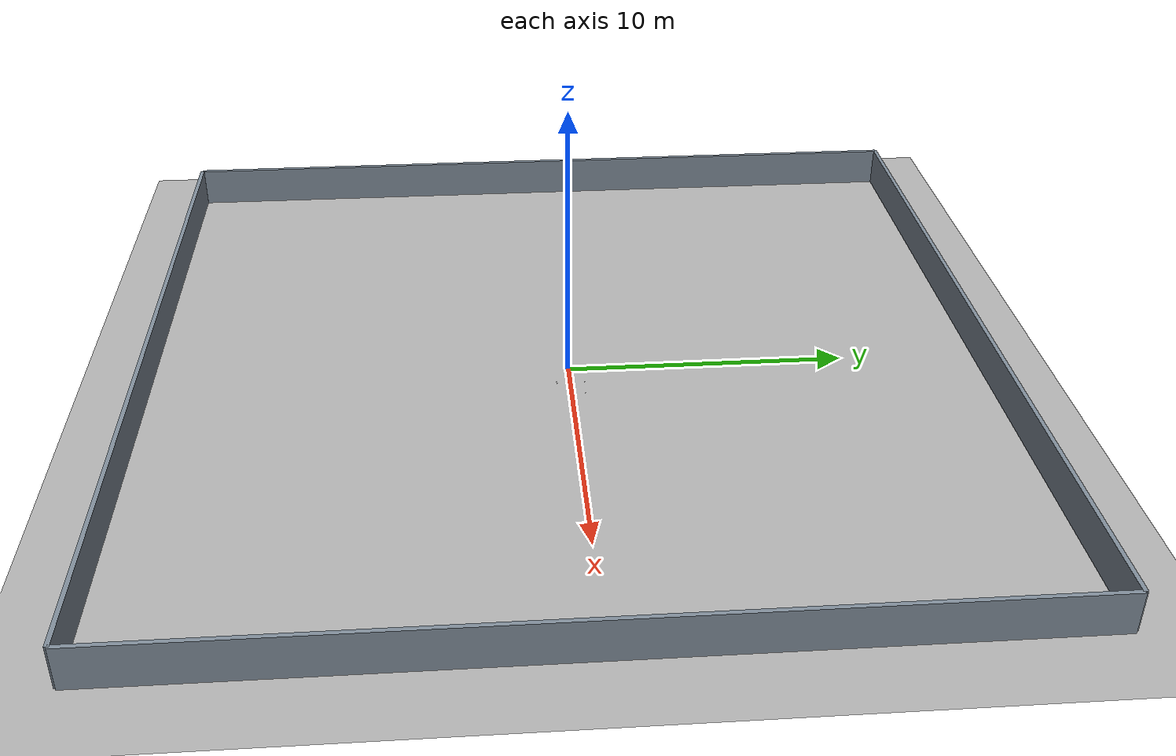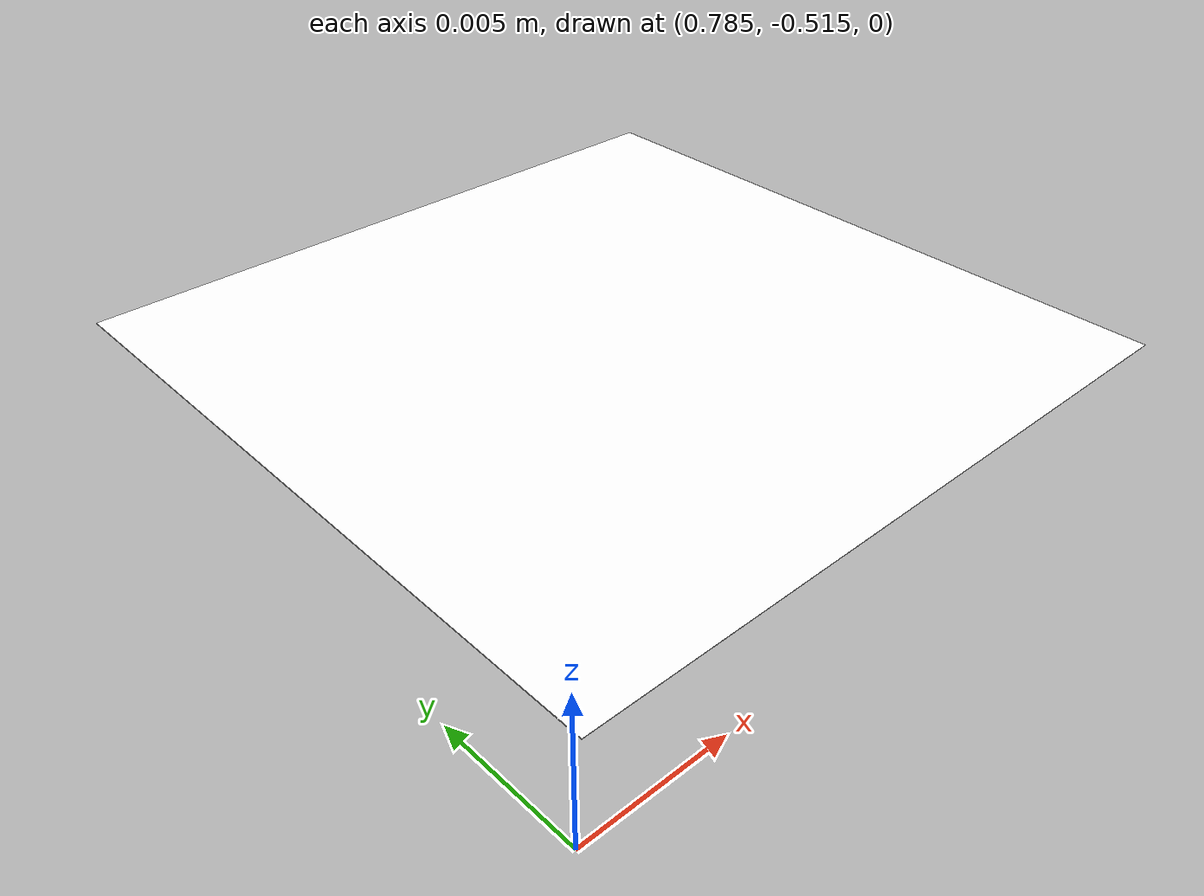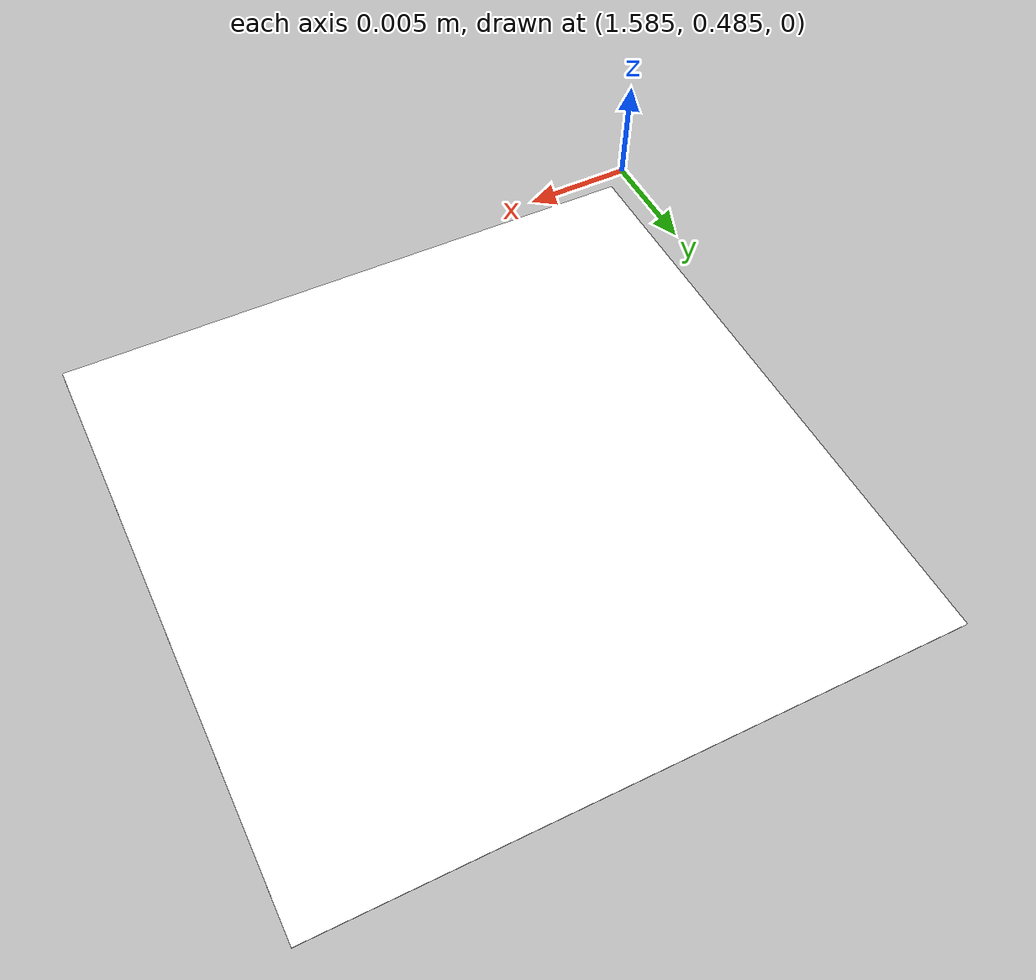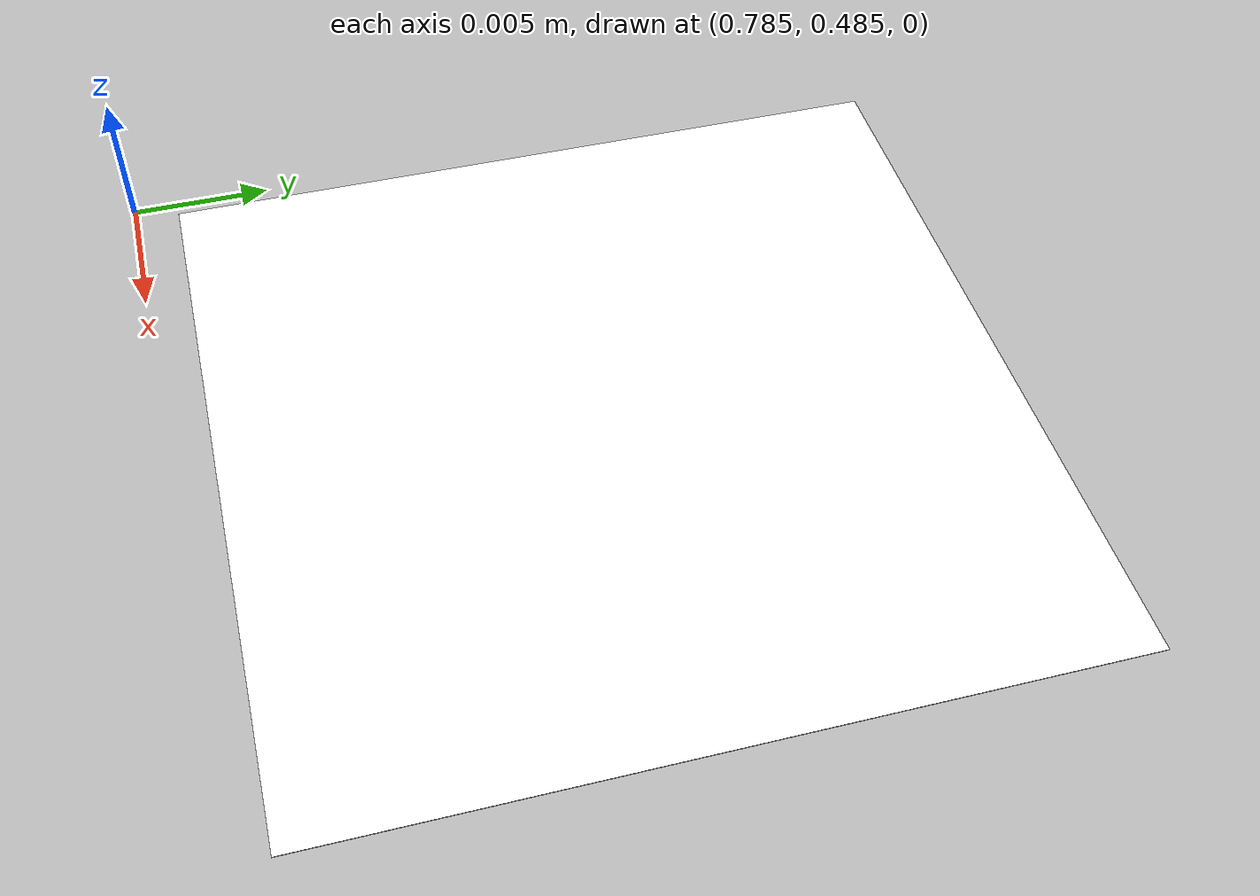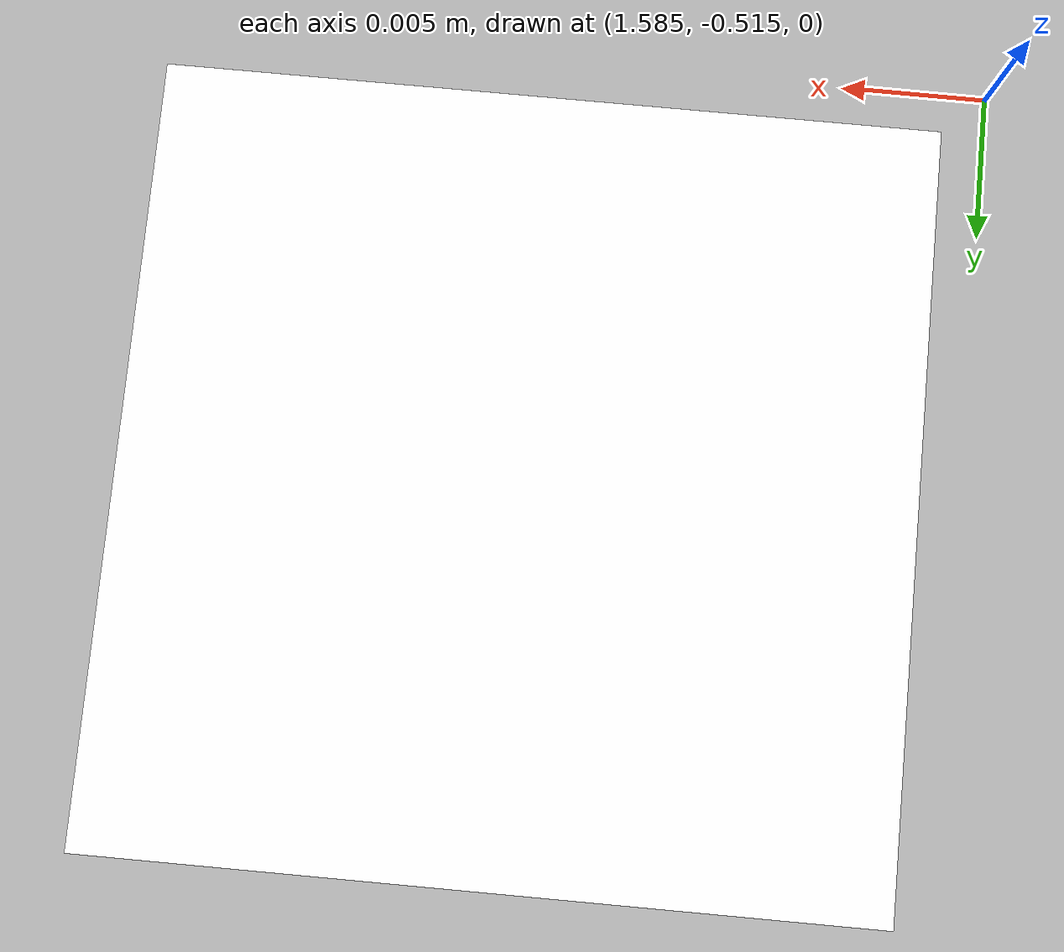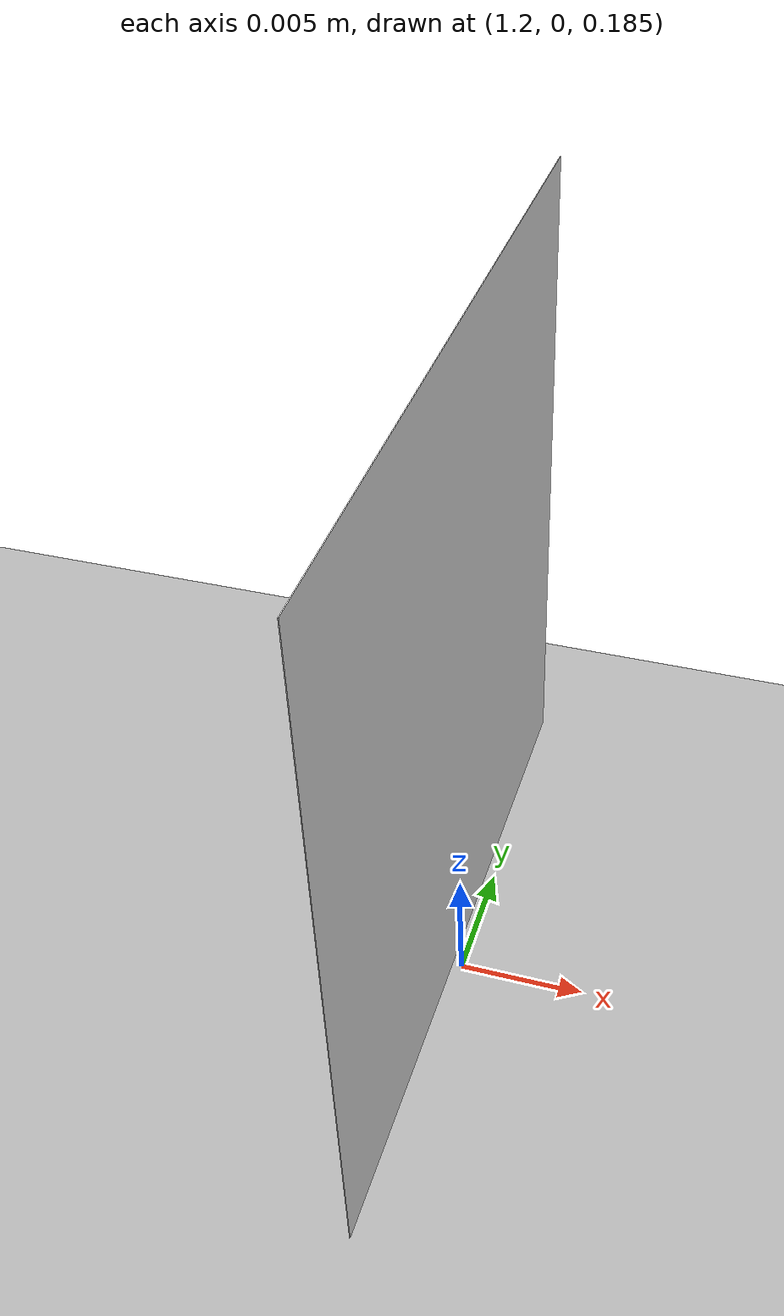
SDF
<?xml version='1.0' encoding='utf-8'?>
<sdf version="1.8">
  <world name="aruco_arena">
    <gravity>0 0 -9.81</gravity>
    <plugin filename="gz-sim-physics-system" name="gz::sim::systems::Physics" />
    <plugin filename="gz-sim-user-commands-system" name="gz::sim::systems::UserCommands" />
    <plugin filename="gz-sim-scene-broadcaster-system" name="gz::sim::systems::SceneBroadcaster" />
    <plugin filename="gz-sim-sensors-system" name="gz::sim::systems::Sensors">
      <render_engine>ogre2</render_engine>
    </plugin>
    <physics type="dart">
      <max_step_size>0.01</max_step_size>
      <real_time_factor>1</real_time_factor>
      <real_time_update_rate>100</real_time_update_rate>
    </physics>
    <model name="aruco_floor_0">
      <static>true</static>
      <pose>0.8 -0.5 0.001 0 0 0</pose>
      <link name="tag">
        <visual name="white_margin">
          <pose>0.0000000000 0.0000000000 0 0 0 0</pose>
          <geometry>
            <plane>
              <normal>0 0 1</normal>
              <size>0.0266666667 0.0266666667</size>
            </plane>
          </geometry>
          <cast_shadows>false</cast_shadows>
          <material>
            <ambient>1 1 1 1</ambient>
            <diffuse>1 1 1 1</diffuse>
            <specular>0 0 0 1</specular>
          </material>
        </visual>
        <visual name="black_0_0">
          <pose>-0.0083333333 0.0083333333 1e-05 0 0 0</pose>
          <geometry>
            <plane>
              <normal>0 0 1</normal>
              <size>0.0033333333 0.0033333333</size>
            </plane>
          </geometry>
          <cast_shadows>false</cast_shadows>
          <material>
            <ambient>0 0 0 1</ambient>
            <diffuse>0 0 0 1</diffuse>
            <specular>0 0 0 1</specular>
          </material>
        </visual>
        <visual name="black_0_1">
          <pose>-0.0050000000 0.0083333333 1e-05 0 0 0</pose>
          <geometry>
            <plane>
              <normal>0 0 1</normal>
              <size>0.0033333333 0.0033333333</size>
            </plane>
          </geometry>
          <cast_shadows>false</cast_shadows>
          <material>
            <ambient>0 0 0 1</ambient>
            <diffuse>0 0 0 1</diffuse>
            <specular>0 0 0 1</specular>
          </material>
        </visual>
        <visual name="black_0_2">
          <pose>-0.0016666667 0.0083333333 1e-05 0 0 0</pose>
          <geometry>
            <plane>
              <normal>0 0 1</normal>
              <size>0.0033333333 0.0033333333</size>
            </plane>
          </geometry>
          <cast_shadows>false</cast_shadows>
          <material>
            <ambient>0 0 0 1</ambient>
            <diffuse>0 0 0 1</diffuse>
            <specular>0 0 0 1</specular>
          </material>
        </visual>
        <visual name="black_0_3">
          <pose>0.0016666667 0.0083333333 1e-05 0 0 0</pose>
          <geometry>
            <plane>
              <normal>0 0 1</normal>
              <size>0.0033333333 0.0033333333</size>
            </plane>
          </geometry>
          <cast_shadows>false</cast_shadows>
          <material>
            <ambient>0 0 0 1</ambient>
            <diffuse>0 0 0 1</diffuse>
            <specular>0 0 0 1</specular>
          </material>
        </visual>
        <visual name="black_0_4">
          <pose>0.0050000000 0.0083333333 1e-05 0 0 0</pose>
          <geometry>
            <plane>
              <normal>0 0 1</normal>
              <size>0.0033333333 0.0033333333</size>
            </plane>
          </geometry>
          <cast_shadows>false</cast_shadows>
          <material>
            <ambient>0 0 0 1</ambient>
            <diffuse>0 0 0 1</diffuse>
            <specular>0 0 0 1</specular>
          </material>
        </visual>
        <visual name="black_0_5">
          <pose>0.0083333333 0.0083333333 1e-05 0 0 0</pose>
          <geometry>
            <plane>
              <normal>0 0 1</normal>
              <size>0.0033333333 0.0033333333</size>
            </plane>
          </geometry>
          <cast_shadows>false</cast_shadows>
          <material>
            <ambient>0 0 0 1</ambient>
            <diffuse>0 0 0 1</diffuse>
            <specular>0 0 0 1</specular>
          </material>
        </visual>
        <visual name="black_1_0">
          <pose>-0.0083333333 0.0050000000 1e-05 0 0 0</pose>
          <geometry>
            <plane>
              <normal>0 0 1</normal>
              <size>0.0033333333 0.0033333333</size>
            </plane>
          </geometry>
          <cast_shadows>false</cast_shadows>
          <material>
            <ambient>0 0 0 1</ambient>
            <diffuse>0 0 0 1</diffuse>
            <specular>0 0 0 1</specular>
          </material>
        </visual>
        <visual name="black_1_2">
          <pose>-0.0016666667 0.0050000000 1e-05 0 0 0</pose>
          <geometry>
            <plane>
              <normal>0 0 1</normal>
              <size>0.0033333333 0.0033333333</size>
            </plane>
          </geometry>
          <cast_shadows>false</cast_shadows>
          <material>
            <ambient>0 0 0 1</ambient>
            <diffuse>0 0 0 1</diffuse>
            <specular>0 0 0 1</specular>
          </material>
        </visual>
        <visual name="black_1_5">
          <pose>0.0083333333 0.0050000000 1e-05 0 0 0</pose>
          <geometry>
            <plane>
              <normal>0 0 1</normal>
              <size>0.0033333333 0.0033333333</size>
            </plane>
          </geometry>
          <cast_shadows>false</cast_shadows>
          <material>
            <ambient>0 0 0 1</ambient>
            <diffuse>0 0 0 1</diffuse>
            <specular>0 0 0 1</specular>
          </material>
        </visual>
        <visual name="black_2_0">
          <pose>-0.0083333333 0.0016666667 1e-05 0 0 0</pose>
          <geometry>
            <plane>
              <normal>0 0 1</normal>
              <size>0.0033333333 0.0033333333</size>
            </plane>
          </geometry>
          <cast_shadows>false</cast_shadows>
          <material>
            <ambient>0 0 0 1</ambient>
            <diffuse>0 0 0 1</diffuse>
            <specular>0 0 0 1</specular>
          </material>
        </visual>
        <visual name="black_2_1">
          <pose>-0.0050000000 0.0016666667 1e-05 0 0 0</pose>
          <geometry>
            <plane>
              <normal>0 0 1</normal>
              <size>0.0033333333 0.0033333333</size>
            </plane>
          </geometry>
          <cast_shadows>false</cast_shadows>
          <material>
            <ambient>0 0 0 1</ambient>
            <diffuse>0 0 0 1</diffuse>
            <specular>0 0 0 1</specular>
          </material>
        </visual>
        <visual name="black_2_3">
          <pose>0.0016666667 0.0016666667 1e-05 0 0 0</pose>
          <geometry>
            <plane>
              <normal>0 0 1</normal>
              <size>0.0033333333 0.0033333333</size>
            </plane>
          </geometry>
          <cast_shadows>false</cast_shadows>
          <material>
            <ambient>0 0 0 1</ambient>
            <diffuse>0 0 0 1</diffuse>
            <specular>0 0 0 1</specular>
          </material>
        </visual>
        <visual name="black_2_5">
          <pose>0.0083333333 0.0016666667 1e-05 0 0 0</pose>
          <geometry>
            <plane>
              <normal>0 0 1</normal>
              <size>0.0033333333 0.0033333333</size>
            </plane>
          </geometry>
          <cast_shadows>false</cast_shadows>
          <material>
            <ambient>0 0 0 1</ambient>
            <diffuse>0 0 0 1</diffuse>
            <specular>0 0 0 1</specular>
          </material>
        </visual>
        <visual name="black_3_0">
          <pose>-0.0083333333 -0.0016666667 1e-05 0 0 0</pose>
          <geometry>
            <plane>
              <normal>0 0 1</normal>
              <size>0.0033333333 0.0033333333</size>
            </plane>
          </geometry>
          <cast_shadows>false</cast_shadows>
          <material>
            <ambient>0 0 0 1</ambient>
            <diffuse>0 0 0 1</diffuse>
            <specular>0 0 0 1</specular>
          </material>
        </visual>
        <visual name="black_3_1">
          <pose>-0.0050000000 -0.0016666667 1e-05 0 0 0</pose>
          <geometry>
            <plane>
              <normal>0 0 1</normal>
              <size>0.0033333333 0.0033333333</size>
            </plane>
          </geometry>
          <cast_shadows>false</cast_shadows>
          <material>
            <ambient>0 0 0 1</ambient>
            <diffuse>0 0 0 1</diffuse>
            <specular>0 0 0 1</specular>
          </material>
        </visual>
        <visual name="black_3_2">
          <pose>-0.0016666667 -0.0016666667 1e-05 0 0 0</pose>
          <geometry>
            <plane>
              <normal>0 0 1</normal>
              <size>0.0033333333 0.0033333333</size>
            </plane>
          </geometry>
          <cast_shadows>false</cast_shadows>
          <material>
            <ambient>0 0 0 1</ambient>
            <diffuse>0 0 0 1</diffuse>
            <specular>0 0 0 1</specular>
          </material>
        </visual>
        <visual name="black_3_5">
          <pose>0.0083333333 -0.0016666667 1e-05 0 0 0</pose>
          <geometry>
            <plane>
              <normal>0 0 1</normal>
              <size>0.0033333333 0.0033333333</size>
            </plane>
          </geometry>
          <cast_shadows>false</cast_shadows>
          <material>
            <ambient>0 0 0 1</ambient>
            <diffuse>0 0 0 1</diffuse>
            <specular>0 0 0 1</specular>
          </material>
        </visual>
        <visual name="black_4_0">
          <pose>-0.0083333333 -0.0050000000 1e-05 0 0 0</pose>
          <geometry>
            <plane>
              <normal>0 0 1</normal>
              <size>0.0033333333 0.0033333333</size>
            </plane>
          </geometry>
          <cast_shadows>false</cast_shadows>
          <material>
            <ambient>0 0 0 1</ambient>
            <diffuse>0 0 0 1</diffuse>
            <specular>0 0 0 1</specular>
          </material>
        </visual>
        <visual name="black_4_1">
          <pose>-0.0050000000 -0.0050000000 1e-05 0 0 0</pose>
          <geometry>
            <plane>
              <normal>0 0 1</normal>
              <size>0.0033333333 0.0033333333</size>
            </plane>
          </geometry>
          <cast_shadows>false</cast_shadows>
          <material>
            <ambient>0 0 0 1</ambient>
            <diffuse>0 0 0 1</diffuse>
            <specular>0 0 0 1</specular>
          </material>
        </visual>
        <visual name="black_4_2">
          <pose>-0.0016666667 -0.0050000000 1e-05 0 0 0</pose>
          <geometry>
            <plane>
              <normal>0 0 1</normal>
              <size>0.0033333333 0.0033333333</size>
            </plane>
          </geometry>
          <cast_shadows>false</cast_shadows>
          <material>
            <ambient>0 0 0 1</ambient>
            <diffuse>0 0 0 1</diffuse>
            <specular>0 0 0 1</specular>
          </material>
        </visual>
        <visual name="black_4_4">
          <pose>0.0050000000 -0.0050000000 1e-05 0 0 0</pose>
          <geometry>
            <plane>
              <normal>0 0 1</normal>
              <size>0.0033333333 0.0033333333</size>
            </plane>
          </geometry>
          <cast_shadows>false</cast_shadows>
          <material>
            <ambient>0 0 0 1</ambient>
            <diffuse>0 0 0 1</diffuse>
            <specular>0 0 0 1</specular>
          </material>
        </visual>
        <visual name="black_4_5">
          <pose>0.0083333333 -0.0050000000 1e-05 0 0 0</pose>
          <geometry>
            <plane>
              <normal>0 0 1</normal>
              <size>0.0033333333 0.0033333333</size>
            </plane>
          </geometry>
          <cast_shadows>false</cast_shadows>
          <material>
            <ambient>0 0 0 1</ambient>
            <diffuse>0 0 0 1</diffuse>
            <specular>0 0 0 1</specular>
          </material>
        </visual>
        <visual name="black_5_0">
          <pose>-0.0083333333 -0.0083333333 1e-05 0 0 0</pose>
          <geometry>
            <plane>
              <normal>0 0 1</normal>
              <size>0.0033333333 0.0033333333</size>
            </plane>
          </geometry>
          <cast_shadows>false</cast_shadows>
          <material>
            <ambient>0 0 0 1</ambient>
            <diffuse>0 0 0 1</diffuse>
            <specular>0 0 0 1</specular>
          </material>
        </visual>
        <visual name="black_5_1">
          <pose>-0.0050000000 -0.0083333333 1e-05 0 0 0</pose>
          <geometry>
            <plane>
              <normal>0 0 1</normal>
              <size>0.0033333333 0.0033333333</size>
            </plane>
          </geometry>
          <cast_shadows>false</cast_shadows>
          <material>
            <ambient>0 0 0 1</ambient>
            <diffuse>0 0 0 1</diffuse>
            <specular>0 0 0 1</specular>
          </material>
        </visual>
        <visual name="black_5_2">
          <pose>-0.0016666667 -0.0083333333 1e-05 0 0 0</pose>
          <geometry>
            <plane>
              <normal>0 0 1</normal>
              <size>0.0033333333 0.0033333333</size>
            </plane>
          </geometry>
          <cast_shadows>false</cast_shadows>
          <material>
            <ambient>0 0 0 1</ambient>
            <diffuse>0 0 0 1</diffuse>
            <specular>0 0 0 1</specular>
          </material>
        </visual>
        <visual name="black_5_3">
          <pose>0.0016666667 -0.0083333333 1e-05 0 0 0</pose>
          <geometry>
            <plane>
              <normal>0 0 1</normal>
              <size>0.0033333333 0.0033333333</size>
            </plane>
          </geometry>
          <cast_shadows>false</cast_shadows>
          <material>
            <ambient>0 0 0 1</ambient>
            <diffuse>0 0 0 1</diffuse>
            <specular>0 0 0 1</specular>
          </material>
        </visual>
        <visual name="black_5_4">
          <pose>0.0050000000 -0.0083333333 1e-05 0 0 0</pose>
          <geometry>
            <plane>
              <normal>0 0 1</normal>
              <size>0.0033333333 0.0033333333</size>
            </plane>
          </geometry>
          <cast_shadows>false</cast_shadows>
          <material>
            <ambient>0 0 0 1</ambient>
            <diffuse>0 0 0 1</diffuse>
            <specular>0 0 0 1</specular>
          </material>
        </visual>
        <visual name="black_5_5">
          <pose>0.0083333333 -0.0083333333 1e-05 0 0 0</pose>
          <geometry>
            <plane>
              <normal>0 0 1</normal>
              <size>0.0033333333 0.0033333333</size>
            </plane>
          </geometry>
          <cast_shadows>false</cast_shadows>
          <material>
            <ambient>0 0 0 1</ambient>
            <diffuse>0 0 0 1</diffuse>
            <specular>0 0 0 1</specular>
          </material>
        </visual>
      </link>
    </model>
    <model name="aruco_floor_1">
      <static>true</static>
      <pose>0.8 0.5 0.001 0 0 0</pose>
      <link name="tag">
        <visual name="white_margin">
          <pose>0.0000000000 0.0000000000 0 0 0 0</pose>
          <geometry>
            <plane>
              <normal>0 0 1</normal>
              <size>0.0266666667 0.0266666667</size>
            </plane>
          </geometry>
          <cast_shadows>false</cast_shadows>
          <material>
            <ambient>1 1 1 1</ambient>
            <diffuse>1 1 1 1</diffuse>
            <specular>0 0 0 1</specular>
          </material>
        </visual>
        <visual name="black_0_0">
          <pose>-0.0083333333 0.0083333333 1e-05 0 0 0</pose>
          <geometry>
            <plane>
              <normal>0 0 1</normal>
              <size>0.0033333333 0.0033333333</size>
            </plane>
          </geometry>
          <cast_shadows>false</cast_shadows>
          <material>
            <ambient>0 0 0 1</ambient>
            <diffuse>0 0 0 1</diffuse>
            <specular>0 0 0 1</specular>
          </material>
        </visual>
        <visual name="black_0_1">
          <pose>-0.0050000000 0.0083333333 1e-05 0 0 0</pose>
          <geometry>
            <plane>
              <normal>0 0 1</normal>
              <size>0.0033333333 0.0033333333</size>
            </plane>
          </geometry>
          <cast_shadows>false</cast_shadows>
          <material>
            <ambient>0 0 0 1</ambient>
            <diffuse>0 0 0 1</diffuse>
            <specular>0 0 0 1</specular>
          </material>
        </visual>
        <visual name="black_0_2">
          <pose>-0.0016666667 0.0083333333 1e-05 0 0 0</pose>
          <geometry>
            <plane>
              <normal>0 0 1</normal>
              <size>0.0033333333 0.0033333333</size>
            </plane>
          </geometry>
          <cast_shadows>false</cast_shadows>
          <material>
            <ambient>0 0 0 1</ambient>
            <diffuse>0 0 0 1</diffuse>
            <specular>0 0 0 1</specular>
          </material>
        </visual>
        <visual name="black_0_3">
          <pose>0.0016666667 0.0083333333 1e-05 0 0 0</pose>
          <geometry>
            <plane>
              <normal>0 0 1</normal>
              <size>0.0033333333 0.0033333333</size>
            </plane>
          </geometry>
          <cast_shadows>false</cast_shadows>
          <material>
            <ambient>0 0 0 1</ambient>
            <diffuse>0 0 0 1</diffuse>
            <specular>0 0 0 1</specular>
          </material>
        </visual>
        <visual name="black_0_4">
          <pose>0.0050000000 0.0083333333 1e-05 0 0 0</pose>
          <geometry>
            <plane>
              <normal>0 0 1</normal>
              <size>0.0033333333 0.0033333333</size>
            </plane>
          </geometry>
          <cast_shadows>false</cast_shadows>
          <material>
            <ambient>0 0 0 1</ambient>
            <diffuse>0 0 0 1</diffuse>
            <specular>0 0 0 1</specular>
          </material>
        </visual>
        <visual name="black_0_5">
          <pose>0.0083333333 0.0083333333 1e-05 0 0 0</pose>
          <geometry>
            <plane>
              <normal>0 0 1</normal>
              <size>0.0033333333 0.0033333333</size>
            </plane>
          </geometry>
          <cast_shadows>false</cast_shadows>
          <material>
            <ambient>0 0 0 1</ambient>
            <diffuse>0 0 0 1</diffuse>
            <specular>0 0 0 1</specular>
          </material>
        </visual>
        <visual name="black_1_0">
          <pose>-0.0083333333 0.0050000000 1e-05 0 0 0</pose>
          <geometry>
            <plane>
              <normal>0 0 1</normal>
              <size>0.0033333333 0.0033333333</size>
            </plane>
          </geometry>
          <cast_shadows>false</cast_shadows>
          <material>
            <ambient>0 0 0 1</ambient>
            <diffuse>0 0 0 1</diffuse>
            <specular>0 0 0 1</specular>
          </material>
        </visual>
        <visual name="black_1_1">
          <pose>-0.0050000000 0.0050000000 1e-05 0 0 0</pose>
          <geometry>
            <plane>
              <normal>0 0 1</normal>
              <size>0.0033333333 0.0033333333</size>
            </plane>
          </geometry>
          <cast_shadows>false</cast_shadows>
          <material>
            <ambient>0 0 0 1</ambient>
            <diffuse>0 0 0 1</diffuse>
            <specular>0 0 0 1</specular>
          </material>
        </visual>
        <visual name="black_1_2">
          <pose>-0.0016666667 0.0050000000 1e-05 0 0 0</pose>
          <geometry>
            <plane>
              <normal>0 0 1</normal>
              <size>0.0033333333 0.0033333333</size>
            </plane>
          </geometry>
          <cast_shadows>false</cast_shadows>
          <material>
            <ambient>0 0 0 1</ambient>
            <diffuse>0 0 0 1</diffuse>
            <specular>0 0 0 1</specular>
          </material>
        </visual>
        <visual name="black_1_3">
          <pose>0.0016666667 0.0050000000 1e-05 0 0 0</pose>
          <geometry>
            <plane>
              <normal>0 0 1</normal>
              <size>0.0033333333 0.0033333333</size>
            </plane>
          </geometry>
          <cast_shadows>false</cast_shadows>
          <material>
            <ambient>0 0 0 1</ambient>
            <diffuse>0 0 0 1</diffuse>
            <specular>0 0 0 1</specular>
          </material>
        </visual>
        <visual name="black_1_4">
          <pose>0.0050000000 0.0050000000 1e-05 0 0 0</pose>
          <geometry>
            <plane>
              <normal>0 0 1</normal>
              <size>0.0033333333 0.0033333333</size>
            </plane>
          </geometry>
          <cast_shadows>false</cast_shadows>
          <material>
            <ambient>0 0 0 1</ambient>
            <diffuse>0 0 0 1</diffuse>
            <specular>0 0 0 1</specular>
          </material>
        </visual>
        <visual name="black_1_5">
          <pose>0.0083333333 0.0050000000 1e-05 0 0 0</pose>
          <geometry>
            <plane>
              <normal>0 0 1</normal>
              <size>0.0033333333 0.0033333333</size>
            </plane>
          </geometry>
          <cast_shadows>false</cast_shadows>
          <material>
            <ambient>0 0 0 1</ambient>
            <diffuse>0 0 0 1</diffuse>
            <specular>0 0 0 1</specular>
          </material>
        </visual>
        <visual name="black_2_0">
          <pose>-0.0083333333 0.0016666667 1e-05 0 0 0</pose>
          <geometry>
            <plane>
              <normal>0 0 1</normal>
              <size>0.0033333333 0.0033333333</size>
            </plane>
          </geometry>
          <cast_shadows>false</cast_shadows>
          <material>
            <ambient>0 0 0 1</ambient>
            <diffuse>0 0 0 1</diffuse>
            <specular>0 0 0 1</specular>
          </material>
        </visual>
        <visual name="black_2_5">
          <pose>0.0083333333 0.0016666667 1e-05 0 0 0</pose>
          <geometry>
            <plane>
              <normal>0 0 1</normal>
              <size>0.0033333333 0.0033333333</size>
            </plane>
          </geometry>
          <cast_shadows>false</cast_shadows>
          <material>
            <ambient>0 0 0 1</ambient>
            <diffuse>0 0 0 1</diffuse>
            <specular>0 0 0 1</specular>
          </material>
        </visual>
        <visual name="black_3_0">
          <pose>-0.0083333333 -0.0016666667 1e-05 0 0 0</pose>
          <geometry>
            <plane>
              <normal>0 0 1</normal>
              <size>0.0033333333 0.0033333333</size>
            </plane>
          </geometry>
          <cast_shadows>false</cast_shadows>
          <material>
            <ambient>0 0 0 1</ambient>
            <diffuse>0 0 0 1</diffuse>
            <specular>0 0 0 1</specular>
          </material>
        </visual>
        <visual name="black_3_2">
          <pose>-0.0016666667 -0.0016666667 1e-05 0 0 0</pose>
          <geometry>
            <plane>
              <normal>0 0 1</normal>
              <size>0.0033333333 0.0033333333</size>
            </plane>
          </geometry>
          <cast_shadows>false</cast_shadows>
          <material>
            <ambient>0 0 0 1</ambient>
            <diffuse>0 0 0 1</diffuse>
            <specular>0 0 0 1</specular>
          </material>
        </visual>
        <visual name="black_3_3">
          <pose>0.0016666667 -0.0016666667 1e-05 0 0 0</pose>
          <geometry>
            <plane>
              <normal>0 0 1</normal>
              <size>0.0033333333 0.0033333333</size>
            </plane>
          </geometry>
          <cast_shadows>false</cast_shadows>
          <material>
            <ambient>0 0 0 1</ambient>
            <diffuse>0 0 0 1</diffuse>
            <specular>0 0 0 1</specular>
          </material>
        </visual>
        <visual name="black_3_5">
          <pose>0.0083333333 -0.0016666667 1e-05 0 0 0</pose>
          <geometry>
            <plane>
              <normal>0 0 1</normal>
              <size>0.0033333333 0.0033333333</size>
            </plane>
          </geometry>
          <cast_shadows>false</cast_shadows>
          <material>
            <ambient>0 0 0 1</ambient>
            <diffuse>0 0 0 1</diffuse>
            <specular>0 0 0 1</specular>
          </material>
        </visual>
        <visual name="black_4_0">
          <pose>-0.0083333333 -0.0050000000 1e-05 0 0 0</pose>
          <geometry>
            <plane>
              <normal>0 0 1</normal>
              <size>0.0033333333 0.0033333333</size>
            </plane>
          </geometry>
          <cast_shadows>false</cast_shadows>
          <material>
            <ambient>0 0 0 1</ambient>
            <diffuse>0 0 0 1</diffuse>
            <specular>0 0 0 1</specular>
          </material>
        </visual>
        <visual name="black_4_2">
          <pose>-0.0016666667 -0.0050000000 1e-05 0 0 0</pose>
          <geometry>
            <plane>
              <normal>0 0 1</normal>
              <size>0.0033333333 0.0033333333</size>
            </plane>
          </geometry>
          <cast_shadows>false</cast_shadows>
          <material>
            <ambient>0 0 0 1</ambient>
            <diffuse>0 0 0 1</diffuse>
            <specular>0 0 0 1</specular>
          </material>
        </visual>
        <visual name="black_4_4">
          <pose>0.0050000000 -0.0050000000 1e-05 0 0 0</pose>
          <geometry>
            <plane>
              <normal>0 0 1</normal>
              <size>0.0033333333 0.0033333333</size>
            </plane>
          </geometry>
          <cast_shadows>false</cast_shadows>
          <material>
            <ambient>0 0 0 1</ambient>
            <diffuse>0 0 0 1</diffuse>
            <specular>0 0 0 1</specular>
          </material>
        </visual>
        <visual name="black_4_5">
          <pose>0.0083333333 -0.0050000000 1e-05 0 0 0</pose>
          <geometry>
            <plane>
              <normal>0 0 1</normal>
              <size>0.0033333333 0.0033333333</size>
            </plane>
          </geometry>
          <cast_shadows>false</cast_shadows>
          <material>
            <ambient>0 0 0 1</ambient>
            <diffuse>0 0 0 1</diffuse>
            <specular>0 0 0 1</specular>
          </material>
        </visual>
        <visual name="black_5_0">
          <pose>-0.0083333333 -0.0083333333 1e-05 0 0 0</pose>
          <geometry>
            <plane>
              <normal>0 0 1</normal>
              <size>0.0033333333 0.0033333333</size>
            </plane>
          </geometry>
          <cast_shadows>false</cast_shadows>
          <material>
            <ambient>0 0 0 1</ambient>
            <diffuse>0 0 0 1</diffuse>
            <specular>0 0 0 1</specular>
          </material>
        </visual>
        <visual name="black_5_1">
          <pose>-0.0050000000 -0.0083333333 1e-05 0 0 0</pose>
          <geometry>
            <plane>
              <normal>0 0 1</normal>
              <size>0.0033333333 0.0033333333</size>
            </plane>
          </geometry>
          <cast_shadows>false</cast_shadows>
          <material>
            <ambient>0 0 0 1</ambient>
            <diffuse>0 0 0 1</diffuse>
            <specular>0 0 0 1</specular>
          </material>
        </visual>
        <visual name="black_5_2">
          <pose>-0.0016666667 -0.0083333333 1e-05 0 0 0</pose>
          <geometry>
            <plane>
              <normal>0 0 1</normal>
              <size>0.0033333333 0.0033333333</size>
            </plane>
          </geometry>
          <cast_shadows>false</cast_shadows>
          <material>
            <ambient>0 0 0 1</ambient>
            <diffuse>0 0 0 1</diffuse>
            <specular>0 0 0 1</specular>
          </material>
        </visual>
        <visual name="black_5_3">
          <pose>0.0016666667 -0.0083333333 1e-05 0 0 0</pose>
          <geometry>
            <plane>
              <normal>0 0 1</normal>
              <size>0.0033333333 0.0033333333</size>
            </plane>
          </geometry>
          <cast_shadows>false</cast_shadows>
          <material>
            <ambient>0 0 0 1</ambient>
            <diffuse>0 0 0 1</diffuse>
            <specular>0 0 0 1</specular>
          </material>
        </visual>
        <visual name="black_5_4">
          <pose>0.0050000000 -0.0083333333 1e-05 0 0 0</pose>
          <geometry>
            <plane>
              <normal>0 0 1</normal>
              <size>0.0033333333 0.0033333333</size>
            </plane>
          </geometry>
          <cast_shadows>false</cast_shadows>
          <material>
            <ambient>0 0 0 1</ambient>
            <diffuse>0 0 0 1</diffuse>
            <specular>0 0 0 1</specular>
          </material>
        </visual>
        <visual name="black_5_5">
          <pose>0.0083333333 -0.0083333333 1e-05 0 0 0</pose>
          <geometry>
            <plane>
              <normal>0 0 1</normal>
              <size>0.0033333333 0.0033333333</size>
            </plane>
          </geometry>
          <cast_shadows>false</cast_shadows>
          <material>
            <ambient>0 0 0 1</ambient>
            <diffuse>0 0 0 1</diffuse>
            <specular>0 0 0 1</specular>
          </material>
        </visual>
      </link>
    </model>
    <model name="aruco_floor_2">
      <static>true</static>
      <pose>1.6 -0.5 0.001 0 0 0</pose>
      <link name="tag">
        <visual name="white_margin">
          <pose>0.0000000000 0.0000000000 0 0 0 0</pose>
          <geometry>
            <plane>
              <normal>0 0 1</normal>
              <size>0.0266666667 0.0266666667</size>
            </plane>
          </geometry>
          <cast_shadows>false</cast_shadows>
          <material>
            <ambient>1 1 1 1</ambient>
            <diffuse>1 1 1 1</diffuse>
            <specular>0 0 0 1</specular>
          </material>
        </visual>
        <visual name="black_0_0">
          <pose>-0.0083333333 0.0083333333 1e-05 0 0 0</pose>
          <geometry>
            <plane>
              <normal>0 0 1</normal>
              <size>0.0033333333 0.0033333333</size>
            </plane>
          </geometry>
          <cast_shadows>false</cast_shadows>
          <material>
            <ambient>0 0 0 1</ambient>
            <diffuse>0 0 0 1</diffuse>
            <specular>0 0 0 1</specular>
          </material>
        </visual>
        <visual name="black_0_1">
          <pose>-0.0050000000 0.0083333333 1e-05 0 0 0</pose>
          <geometry>
            <plane>
              <normal>0 0 1</normal>
              <size>0.0033333333 0.0033333333</size>
            </plane>
          </geometry>
          <cast_shadows>false</cast_shadows>
          <material>
            <ambient>0 0 0 1</ambient>
            <diffuse>0 0 0 1</diffuse>
            <specular>0 0 0 1</specular>
          </material>
        </visual>
        <visual name="black_0_2">
          <pose>-0.0016666667 0.0083333333 1e-05 0 0 0</pose>
          <geometry>
            <plane>
              <normal>0 0 1</normal>
              <size>0.0033333333 0.0033333333</size>
            </plane>
          </geometry>
          <cast_shadows>false</cast_shadows>
          <material>
            <ambient>0 0 0 1</ambient>
            <diffuse>0 0 0 1</diffuse>
            <specular>0 0 0 1</specular>
          </material>
        </visual>
        <visual name="black_0_3">
          <pose>0.0016666667 0.0083333333 1e-05 0 0 0</pose>
          <geometry>
            <plane>
              <normal>0 0 1</normal>
              <size>0.0033333333 0.0033333333</size>
            </plane>
          </geometry>
          <cast_shadows>false</cast_shadows>
          <material>
            <ambient>0 0 0 1</ambient>
            <diffuse>0 0 0 1</diffuse>
            <specular>0 0 0 1</specular>
          </material>
        </visual>
        <visual name="black_0_4">
          <pose>0.0050000000 0.0083333333 1e-05 0 0 0</pose>
          <geometry>
            <plane>
              <normal>0 0 1</normal>
              <size>0.0033333333 0.0033333333</size>
            </plane>
          </geometry>
          <cast_shadows>false</cast_shadows>
          <material>
            <ambient>0 0 0 1</ambient>
            <diffuse>0 0 0 1</diffuse>
            <specular>0 0 0 1</specular>
          </material>
        </visual>
        <visual name="black_0_5">
          <pose>0.0083333333 0.0083333333 1e-05 0 0 0</pose>
          <geometry>
            <plane>
              <normal>0 0 1</normal>
              <size>0.0033333333 0.0033333333</size>
            </plane>
          </geometry>
          <cast_shadows>false</cast_shadows>
          <material>
            <ambient>0 0 0 1</ambient>
            <diffuse>0 0 0 1</diffuse>
            <specular>0 0 0 1</specular>
          </material>
        </visual>
        <visual name="black_1_0">
          <pose>-0.0083333333 0.0050000000 1e-05 0 0 0</pose>
          <geometry>
            <plane>
              <normal>0 0 1</normal>
              <size>0.0033333333 0.0033333333</size>
            </plane>
          </geometry>
          <cast_shadows>false</cast_shadows>
          <material>
            <ambient>0 0 0 1</ambient>
            <diffuse>0 0 0 1</diffuse>
            <specular>0 0 0 1</specular>
          </material>
        </visual>
        <visual name="black_1_1">
          <pose>-0.0050000000 0.0050000000 1e-05 0 0 0</pose>
          <geometry>
            <plane>
              <normal>0 0 1</normal>
              <size>0.0033333333 0.0033333333</size>
            </plane>
          </geometry>
          <cast_shadows>false</cast_shadows>
          <material>
            <ambient>0 0 0 1</ambient>
            <diffuse>0 0 0 1</diffuse>
            <specular>0 0 0 1</specular>
          </material>
        </visual>
        <visual name="black_1_2">
          <pose>-0.0016666667 0.0050000000 1e-05 0 0 0</pose>
          <geometry>
            <plane>
              <normal>0 0 1</normal>
              <size>0.0033333333 0.0033333333</size>
            </plane>
          </geometry>
          <cast_shadows>false</cast_shadows>
          <material>
            <ambient>0 0 0 1</ambient>
            <diffuse>0 0 0 1</diffuse>
            <specular>0 0 0 1</specular>
          </material>
        </visual>
        <visual name="black_1_5">
          <pose>0.0083333333 0.0050000000 1e-05 0 0 0</pose>
          <geometry>
            <plane>
              <normal>0 0 1</normal>
              <size>0.0033333333 0.0033333333</size>
            </plane>
          </geometry>
          <cast_shadows>false</cast_shadows>
          <material>
            <ambient>0 0 0 1</ambient>
            <diffuse>0 0 0 1</diffuse>
            <specular>0 0 0 1</specular>
          </material>
        </visual>
        <visual name="black_2_0">
          <pose>-0.0083333333 0.0016666667 1e-05 0 0 0</pose>
          <geometry>
            <plane>
              <normal>0 0 1</normal>
              <size>0.0033333333 0.0033333333</size>
            </plane>
          </geometry>
          <cast_shadows>false</cast_shadows>
          <material>
            <ambient>0 0 0 1</ambient>
            <diffuse>0 0 0 1</diffuse>
            <specular>0 0 0 1</specular>
          </material>
        </visual>
        <visual name="black_2_1">
          <pose>-0.0050000000 0.0016666667 1e-05 0 0 0</pose>
          <geometry>
            <plane>
              <normal>0 0 1</normal>
              <size>0.0033333333 0.0033333333</size>
            </plane>
          </geometry>
          <cast_shadows>false</cast_shadows>
          <material>
            <ambient>0 0 0 1</ambient>
            <diffuse>0 0 0 1</diffuse>
            <specular>0 0 0 1</specular>
          </material>
        </visual>
        <visual name="black_2_2">
          <pose>-0.0016666667 0.0016666667 1e-05 0 0 0</pose>
          <geometry>
            <plane>
              <normal>0 0 1</normal>
              <size>0.0033333333 0.0033333333</size>
            </plane>
          </geometry>
          <cast_shadows>false</cast_shadows>
          <material>
            <ambient>0 0 0 1</ambient>
            <diffuse>0 0 0 1</diffuse>
            <specular>0 0 0 1</specular>
          </material>
        </visual>
        <visual name="black_2_5">
          <pose>0.0083333333 0.0016666667 1e-05 0 0 0</pose>
          <geometry>
            <plane>
              <normal>0 0 1</normal>
              <size>0.0033333333 0.0033333333</size>
            </plane>
          </geometry>
          <cast_shadows>false</cast_shadows>
          <material>
            <ambient>0 0 0 1</ambient>
            <diffuse>0 0 0 1</diffuse>
            <specular>0 0 0 1</specular>
          </material>
        </visual>
        <visual name="black_3_0">
          <pose>-0.0083333333 -0.0016666667 1e-05 0 0 0</pose>
          <geometry>
            <plane>
              <normal>0 0 1</normal>
              <size>0.0033333333 0.0033333333</size>
            </plane>
          </geometry>
          <cast_shadows>false</cast_shadows>
          <material>
            <ambient>0 0 0 1</ambient>
            <diffuse>0 0 0 1</diffuse>
            <specular>0 0 0 1</specular>
          </material>
        </visual>
        <visual name="black_3_1">
          <pose>-0.0050000000 -0.0016666667 1e-05 0 0 0</pose>
          <geometry>
            <plane>
              <normal>0 0 1</normal>
              <size>0.0033333333 0.0033333333</size>
            </plane>
          </geometry>
          <cast_shadows>false</cast_shadows>
          <material>
            <ambient>0 0 0 1</ambient>
            <diffuse>0 0 0 1</diffuse>
            <specular>0 0 0 1</specular>
          </material>
        </visual>
        <visual name="black_3_2">
          <pose>-0.0016666667 -0.0016666667 1e-05 0 0 0</pose>
          <geometry>
            <plane>
              <normal>0 0 1</normal>
              <size>0.0033333333 0.0033333333</size>
            </plane>
          </geometry>
          <cast_shadows>false</cast_shadows>
          <material>
            <ambient>0 0 0 1</ambient>
            <diffuse>0 0 0 1</diffuse>
            <specular>0 0 0 1</specular>
          </material>
        </visual>
        <visual name="black_3_4">
          <pose>0.0050000000 -0.0016666667 1e-05 0 0 0</pose>
          <geometry>
            <plane>
              <normal>0 0 1</normal>
              <size>0.0033333333 0.0033333333</size>
            </plane>
          </geometry>
          <cast_shadows>false</cast_shadows>
          <material>
            <ambient>0 0 0 1</ambient>
            <diffuse>0 0 0 1</diffuse>
            <specular>0 0 0 1</specular>
          </material>
        </visual>
        <visual name="black_3_5">
          <pose>0.0083333333 -0.0016666667 1e-05 0 0 0</pose>
          <geometry>
            <plane>
              <normal>0 0 1</normal>
              <size>0.0033333333 0.0033333333</size>
            </plane>
          </geometry>
          <cast_shadows>false</cast_shadows>
          <material>
            <ambient>0 0 0 1</ambient>
            <diffuse>0 0 0 1</diffuse>
            <specular>0 0 0 1</specular>
          </material>
        </visual>
        <visual name="black_4_0">
          <pose>-0.0083333333 -0.0050000000 1e-05 0 0 0</pose>
          <geometry>
            <plane>
              <normal>0 0 1</normal>
              <size>0.0033333333 0.0033333333</size>
            </plane>
          </geometry>
          <cast_shadows>false</cast_shadows>
          <material>
            <ambient>0 0 0 1</ambient>
            <diffuse>0 0 0 1</diffuse>
            <specular>0 0 0 1</specular>
          </material>
        </visual>
        <visual name="black_4_3">
          <pose>0.0016666667 -0.0050000000 1e-05 0 0 0</pose>
          <geometry>
            <plane>
              <normal>0 0 1</normal>
              <size>0.0033333333 0.0033333333</size>
            </plane>
          </geometry>
          <cast_shadows>false</cast_shadows>
          <material>
            <ambient>0 0 0 1</ambient>
            <diffuse>0 0 0 1</diffuse>
            <specular>0 0 0 1</specular>
          </material>
        </visual>
        <visual name="black_4_5">
          <pose>0.0083333333 -0.0050000000 1e-05 0 0 0</pose>
          <geometry>
            <plane>
              <normal>0 0 1</normal>
              <size>0.0033333333 0.0033333333</size>
            </plane>
          </geometry>
          <cast_shadows>false</cast_shadows>
          <material>
            <ambient>0 0 0 1</ambient>
            <diffuse>0 0 0 1</diffuse>
            <specular>0 0 0 1</specular>
          </material>
        </visual>
        <visual name="black_5_0">
          <pose>-0.0083333333 -0.0083333333 1e-05 0 0 0</pose>
          <geometry>
            <plane>
              <normal>0 0 1</normal>
              <size>0.0033333333 0.0033333333</size>
            </plane>
          </geometry>
          <cast_shadows>false</cast_shadows>
          <material>
            <ambient>0 0 0 1</ambient>
            <diffuse>0 0 0 1</diffuse>
            <specular>0 0 0 1</specular>
          </material>
        </visual>
        <visual name="black_5_1">
          <pose>-0.0050000000 -0.0083333333 1e-05 0 0 0</pose>
          <geometry>
            <plane>
              <normal>0 0 1</normal>
              <size>0.0033333333 0.0033333333</size>
            </plane>
          </geometry>
          <cast_shadows>false</cast_shadows>
          <material>
            <ambient>0 0 0 1</ambient>
            <diffuse>0 0 0 1</diffuse>
            <specular>0 0 0 1</specular>
          </material>
        </visual>
        <visual name="black_5_2">
          <pose>-0.0016666667 -0.0083333333 1e-05 0 0 0</pose>
          <geometry>
            <plane>
              <normal>0 0 1</normal>
              <size>0.0033333333 0.0033333333</size>
            </plane>
          </geometry>
          <cast_shadows>false</cast_shadows>
          <material>
            <ambient>0 0 0 1</ambient>
            <diffuse>0 0 0 1</diffuse>
            <specular>0 0 0 1</specular>
          </material>
        </visual>
        <visual name="black_5_3">
          <pose>0.0016666667 -0.0083333333 1e-05 0 0 0</pose>
          <geometry>
            <plane>
              <normal>0 0 1</normal>
              <size>0.0033333333 0.0033333333</size>
            </plane>
          </geometry>
          <cast_shadows>false</cast_shadows>
          <material>
            <ambient>0 0 0 1</ambient>
            <diffuse>0 0 0 1</diffuse>
            <specular>0 0 0 1</specular>
          </material>
        </visual>
        <visual name="black_5_4">
          <pose>0.0050000000 -0.0083333333 1e-05 0 0 0</pose>
          <geometry>
            <plane>
              <normal>0 0 1</normal>
              <size>0.0033333333 0.0033333333</size>
            </plane>
          </geometry>
          <cast_shadows>false</cast_shadows>
          <material>
            <ambient>0 0 0 1</ambient>
            <diffuse>0 0 0 1</diffuse>
            <specular>0 0 0 1</specular>
          </material>
        </visual>
        <visual name="black_5_5">
          <pose>0.0083333333 -0.0083333333 1e-05 0 0 0</pose>
          <geometry>
            <plane>
              <normal>0 0 1</normal>
              <size>0.0033333333 0.0033333333</size>
            </plane>
          </geometry>
          <cast_shadows>false</cast_shadows>
          <material>
            <ambient>0 0 0 1</ambient>
            <diffuse>0 0 0 1</diffuse>
            <specular>0 0 0 1</specular>
          </material>
        </visual>
      </link>
    </model>
    <model name="aruco_floor_3">
      <static>true</static>
      <pose>1.6 0.5 0.001 0 0 0</pose>
      <link name="tag">
        <visual name="white_margin">
          <pose>0.0000000000 0.0000000000 0 0 0 0</pose>
          <geometry>
            <plane>
              <normal>0 0 1</normal>
              <size>0.0266666667 0.0266666667</size>
            </plane>
          </geometry>
          <cast_shadows>false</cast_shadows>
          <material>
            <ambient>1 1 1 1</ambient>
            <diffuse>1 1 1 1</diffuse>
            <specular>0 0 0 1</specular>
          </material>
        </visual>
        <visual name="black_0_0">
          <pose>-0.0083333333 0.0083333333 1e-05 0 0 0</pose>
          <geometry>
            <plane>
              <normal>0 0 1</normal>
              <size>0.0033333333 0.0033333333</size>
            </plane>
          </geometry>
          <cast_shadows>false</cast_shadows>
          <material>
            <ambient>0 0 0 1</ambient>
            <diffuse>0 0 0 1</diffuse>
            <specular>0 0 0 1</specular>
          </material>
        </visual>
        <visual name="black_0_1">
          <pose>-0.0050000000 0.0083333333 1e-05 0 0 0</pose>
          <geometry>
            <plane>
              <normal>0 0 1</normal>
              <size>0.0033333333 0.0033333333</size>
            </plane>
          </geometry>
          <cast_shadows>false</cast_shadows>
          <material>
            <ambient>0 0 0 1</ambient>
            <diffuse>0 0 0 1</diffuse>
            <specular>0 0 0 1</specular>
          </material>
        </visual>
        <visual name="black_0_2">
          <pose>-0.0016666667 0.0083333333 1e-05 0 0 0</pose>
          <geometry>
            <plane>
              <normal>0 0 1</normal>
              <size>0.0033333333 0.0033333333</size>
            </plane>
          </geometry>
          <cast_shadows>false</cast_shadows>
          <material>
            <ambient>0 0 0 1</ambient>
            <diffuse>0 0 0 1</diffuse>
            <specular>0 0 0 1</specular>
          </material>
        </visual>
        <visual name="black_0_3">
          <pose>0.0016666667 0.0083333333 1e-05 0 0 0</pose>
          <geometry>
            <plane>
              <normal>0 0 1</normal>
              <size>0.0033333333 0.0033333333</size>
            </plane>
          </geometry>
          <cast_shadows>false</cast_shadows>
          <material>
            <ambient>0 0 0 1</ambient>
            <diffuse>0 0 0 1</diffuse>
            <specular>0 0 0 1</specular>
          </material>
        </visual>
        <visual name="black_0_4">
          <pose>0.0050000000 0.0083333333 1e-05 0 0 0</pose>
          <geometry>
            <plane>
              <normal>0 0 1</normal>
              <size>0.0033333333 0.0033333333</size>
            </plane>
          </geometry>
          <cast_shadows>false</cast_shadows>
          <material>
            <ambient>0 0 0 1</ambient>
            <diffuse>0 0 0 1</diffuse>
            <specular>0 0 0 1</specular>
          </material>
        </visual>
        <visual name="black_0_5">
          <pose>0.0083333333 0.0083333333 1e-05 0 0 0</pose>
          <geometry>
            <plane>
              <normal>0 0 1</normal>
              <size>0.0033333333 0.0033333333</size>
            </plane>
          </geometry>
          <cast_shadows>false</cast_shadows>
          <material>
            <ambient>0 0 0 1</ambient>
            <diffuse>0 0 0 1</diffuse>
            <specular>0 0 0 1</specular>
          </material>
        </visual>
        <visual name="black_1_0">
          <pose>-0.0083333333 0.0050000000 1e-05 0 0 0</pose>
          <geometry>
            <plane>
              <normal>0 0 1</normal>
              <size>0.0033333333 0.0033333333</size>
            </plane>
          </geometry>
          <cast_shadows>false</cast_shadows>
          <material>
            <ambient>0 0 0 1</ambient>
            <diffuse>0 0 0 1</diffuse>
            <specular>0 0 0 1</specular>
          </material>
        </visual>
        <visual name="black_1_2">
          <pose>-0.0016666667 0.0050000000 1e-05 0 0 0</pose>
          <geometry>
            <plane>
              <normal>0 0 1</normal>
              <size>0.0033333333 0.0033333333</size>
            </plane>
          </geometry>
          <cast_shadows>false</cast_shadows>
          <material>
            <ambient>0 0 0 1</ambient>
            <diffuse>0 0 0 1</diffuse>
            <specular>0 0 0 1</specular>
          </material>
        </visual>
        <visual name="black_1_3">
          <pose>0.0016666667 0.0050000000 1e-05 0 0 0</pose>
          <geometry>
            <plane>
              <normal>0 0 1</normal>
              <size>0.0033333333 0.0033333333</size>
            </plane>
          </geometry>
          <cast_shadows>false</cast_shadows>
          <material>
            <ambient>0 0 0 1</ambient>
            <diffuse>0 0 0 1</diffuse>
            <specular>0 0 0 1</specular>
          </material>
        </visual>
        <visual name="black_1_5">
          <pose>0.0083333333 0.0050000000 1e-05 0 0 0</pose>
          <geometry>
            <plane>
              <normal>0 0 1</normal>
              <size>0.0033333333 0.0033333333</size>
            </plane>
          </geometry>
          <cast_shadows>false</cast_shadows>
          <material>
            <ambient>0 0 0 1</ambient>
            <diffuse>0 0 0 1</diffuse>
            <specular>0 0 0 1</specular>
          </material>
        </visual>
        <visual name="black_2_0">
          <pose>-0.0083333333 0.0016666667 1e-05 0 0 0</pose>
          <geometry>
            <plane>
              <normal>0 0 1</normal>
              <size>0.0033333333 0.0033333333</size>
            </plane>
          </geometry>
          <cast_shadows>false</cast_shadows>
          <material>
            <ambient>0 0 0 1</ambient>
            <diffuse>0 0 0 1</diffuse>
            <specular>0 0 0 1</specular>
          </material>
        </visual>
        <visual name="black_2_2">
          <pose>-0.0016666667 0.0016666667 1e-05 0 0 0</pose>
          <geometry>
            <plane>
              <normal>0 0 1</normal>
              <size>0.0033333333 0.0033333333</size>
            </plane>
          </geometry>
          <cast_shadows>false</cast_shadows>
          <material>
            <ambient>0 0 0 1</ambient>
            <diffuse>0 0 0 1</diffuse>
            <specular>0 0 0 1</specular>
          </material>
        </visual>
        <visual name="black_2_3">
          <pose>0.0016666667 0.0016666667 1e-05 0 0 0</pose>
          <geometry>
            <plane>
              <normal>0 0 1</normal>
              <size>0.0033333333 0.0033333333</size>
            </plane>
          </geometry>
          <cast_shadows>false</cast_shadows>
          <material>
            <ambient>0 0 0 1</ambient>
            <diffuse>0 0 0 1</diffuse>
            <specular>0 0 0 1</specular>
          </material>
        </visual>
        <visual name="black_2_5">
          <pose>0.0083333333 0.0016666667 1e-05 0 0 0</pose>
          <geometry>
            <plane>
              <normal>0 0 1</normal>
              <size>0.0033333333 0.0033333333</size>
            </plane>
          </geometry>
          <cast_shadows>false</cast_shadows>
          <material>
            <ambient>0 0 0 1</ambient>
            <diffuse>0 0 0 1</diffuse>
            <specular>0 0 0 1</specular>
          </material>
        </visual>
        <visual name="black_3_0">
          <pose>-0.0083333333 -0.0016666667 1e-05 0 0 0</pose>
          <geometry>
            <plane>
              <normal>0 0 1</normal>
              <size>0.0033333333 0.0033333333</size>
            </plane>
          </geometry>
          <cast_shadows>false</cast_shadows>
          <material>
            <ambient>0 0 0 1</ambient>
            <diffuse>0 0 0 1</diffuse>
            <specular>0 0 0 1</specular>
          </material>
        </visual>
        <visual name="black_3_1">
          <pose>-0.0050000000 -0.0016666667 1e-05 0 0 0</pose>
          <geometry>
            <plane>
              <normal>0 0 1</normal>
              <size>0.0033333333 0.0033333333</size>
            </plane>
          </geometry>
          <cast_shadows>false</cast_shadows>
          <material>
            <ambient>0 0 0 1</ambient>
            <diffuse>0 0 0 1</diffuse>
            <specular>0 0 0 1</specular>
          </material>
        </visual>
        <visual name="black_3_3">
          <pose>0.0016666667 -0.0016666667 1e-05 0 0 0</pose>
          <geometry>
            <plane>
              <normal>0 0 1</normal>
              <size>0.0033333333 0.0033333333</size>
            </plane>
          </geometry>
          <cast_shadows>false</cast_shadows>
          <material>
            <ambient>0 0 0 1</ambient>
            <diffuse>0 0 0 1</diffuse>
            <specular>0 0 0 1</specular>
          </material>
        </visual>
        <visual name="black_3_4">
          <pose>0.0050000000 -0.0016666667 1e-05 0 0 0</pose>
          <geometry>
            <plane>
              <normal>0 0 1</normal>
              <size>0.0033333333 0.0033333333</size>
            </plane>
          </geometry>
          <cast_shadows>false</cast_shadows>
          <material>
            <ambient>0 0 0 1</ambient>
            <diffuse>0 0 0 1</diffuse>
            <specular>0 0 0 1</specular>
          </material>
        </visual>
        <visual name="black_3_5">
          <pose>0.0083333333 -0.0016666667 1e-05 0 0 0</pose>
          <geometry>
            <plane>
              <normal>0 0 1</normal>
              <size>0.0033333333 0.0033333333</size>
            </plane>
          </geometry>
          <cast_shadows>false</cast_shadows>
          <material>
            <ambient>0 0 0 1</ambient>
            <diffuse>0 0 0 1</diffuse>
            <specular>0 0 0 1</specular>
          </material>
        </visual>
        <visual name="black_4_0">
          <pose>-0.0083333333 -0.0050000000 1e-05 0 0 0</pose>
          <geometry>
            <plane>
              <normal>0 0 1</normal>
              <size>0.0033333333 0.0033333333</size>
            </plane>
          </geometry>
          <cast_shadows>false</cast_shadows>
          <material>
            <ambient>0 0 0 1</ambient>
            <diffuse>0 0 0 1</diffuse>
            <specular>0 0 0 1</specular>
          </material>
        </visual>
        <visual name="black_4_1">
          <pose>-0.0050000000 -0.0050000000 1e-05 0 0 0</pose>
          <geometry>
            <plane>
              <normal>0 0 1</normal>
              <size>0.0033333333 0.0033333333</size>
            </plane>
          </geometry>
          <cast_shadows>false</cast_shadows>
          <material>
            <ambient>0 0 0 1</ambient>
            <diffuse>0 0 0 1</diffuse>
            <specular>0 0 0 1</specular>
          </material>
        </visual>
        <visual name="black_4_4">
          <pose>0.0050000000 -0.0050000000 1e-05 0 0 0</pose>
          <geometry>
            <plane>
              <normal>0 0 1</normal>
              <size>0.0033333333 0.0033333333</size>
            </plane>
          </geometry>
          <cast_shadows>false</cast_shadows>
          <material>
            <ambient>0 0 0 1</ambient>
            <diffuse>0 0 0 1</diffuse>
            <specular>0 0 0 1</specular>
          </material>
        </visual>
        <visual name="black_4_5">
          <pose>0.0083333333 -0.0050000000 1e-05 0 0 0</pose>
          <geometry>
            <plane>
              <normal>0 0 1</normal>
              <size>0.0033333333 0.0033333333</size>
            </plane>
          </geometry>
          <cast_shadows>false</cast_shadows>
          <material>
            <ambient>0 0 0 1</ambient>
            <diffuse>0 0 0 1</diffuse>
            <specular>0 0 0 1</specular>
          </material>
        </visual>
        <visual name="black_5_0">
          <pose>-0.0083333333 -0.0083333333 1e-05 0 0 0</pose>
          <geometry>
            <plane>
              <normal>0 0 1</normal>
              <size>0.0033333333 0.0033333333</size>
            </plane>
          </geometry>
          <cast_shadows>false</cast_shadows>
          <material>
            <ambient>0 0 0 1</ambient>
            <diffuse>0 0 0 1</diffuse>
            <specular>0 0 0 1</specular>
          </material>
        </visual>
        <visual name="black_5_1">
          <pose>-0.0050000000 -0.0083333333 1e-05 0 0 0</pose>
          <geometry>
            <plane>
              <normal>0 0 1</normal>
              <size>0.0033333333 0.0033333333</size>
            </plane>
          </geometry>
          <cast_shadows>false</cast_shadows>
          <material>
            <ambient>0 0 0 1</ambient>
            <diffuse>0 0 0 1</diffuse>
            <specular>0 0 0 1</specular>
          </material>
        </visual>
        <visual name="black_5_2">
          <pose>-0.0016666667 -0.0083333333 1e-05 0 0 0</pose>
          <geometry>
            <plane>
              <normal>0 0 1</normal>
              <size>0.0033333333 0.0033333333</size>
            </plane>
          </geometry>
          <cast_shadows>false</cast_shadows>
          <material>
            <ambient>0 0 0 1</ambient>
            <diffuse>0 0 0 1</diffuse>
            <specular>0 0 0 1</specular>
          </material>
        </visual>
        <visual name="black_5_3">
          <pose>0.0016666667 -0.0083333333 1e-05 0 0 0</pose>
          <geometry>
            <plane>
              <normal>0 0 1</normal>
              <size>0.0033333333 0.0033333333</size>
            </plane>
          </geometry>
          <cast_shadows>false</cast_shadows>
          <material>
            <ambient>0 0 0 1</ambient>
            <diffuse>0 0 0 1</diffuse>
            <specular>0 0 0 1</specular>
          </material>
        </visual>
        <visual name="black_5_4">
          <pose>0.0050000000 -0.0083333333 1e-05 0 0 0</pose>
          <geometry>
            <plane>
              <normal>0 0 1</normal>
              <size>0.0033333333 0.0033333333</size>
            </plane>
          </geometry>
          <cast_shadows>false</cast_shadows>
          <material>
            <ambient>0 0 0 1</ambient>
            <diffuse>0 0 0 1</diffuse>
            <specular>0 0 0 1</specular>
          </material>
        </visual>
        <visual name="black_5_5">
          <pose>0.0083333333 -0.0083333333 1e-05 0 0 0</pose>
          <geometry>
            <plane>
              <normal>0 0 1</normal>
              <size>0.0033333333 0.0033333333</size>
            </plane>
          </geometry>
          <cast_shadows>false</cast_shadows>
          <material>
            <ambient>0 0 0 1</ambient>
            <diffuse>0 0 0 1</diffuse>
            <specular>0 0 0 1</specular>
          </material>
        </visual>
      </link>
    </model>
    <model name="aruco_upright_0">
      <static>true</static>
      <pose>1.2 -0.5 0.20 0 -1.57079632679 0</pose>
      <link name="tag">
        <visual name="white_margin">
          <pose>0.0000000000 0.0000000000 0 0 0 0</pose>
          <geometry>
            <plane>
              <normal>0 0 1</normal>
              <size>0.0266666667 0.0266666667</size>
            </plane>
          </geometry>
          <cast_shadows>false</cast_shadows>
          <material>
            <ambient>1 1 1 1</ambient>
            <diffuse>1 1 1 1</diffuse>
            <specular>0 0 0 1</specular>
          </material>
        </visual>
        <visual name="black_0_0">
          <pose>-0.0083333333 0.0083333333 1e-05 0 0 0</pose>
          <geometry>
            <plane>
              <normal>0 0 1</normal>
              <size>0.0033333333 0.0033333333</size>
            </plane>
          </geometry>
          <cast_shadows>false</cast_shadows>
          <material>
            <ambient>0 0 0 1</ambient>
            <diffuse>0 0 0 1</diffuse>
            <specular>0 0 0 1</specular>
          </material>
        </visual>
        <visual name="black_0_1">
          <pose>-0.0050000000 0.0083333333 1e-05 0 0 0</pose>
          <geometry>
            <plane>
              <normal>0 0 1</normal>
              <size>0.0033333333 0.0033333333</size>
            </plane>
          </geometry>
          <cast_shadows>false</cast_shadows>
          <material>
            <ambient>0 0 0 1</ambient>
            <diffuse>0 0 0 1</diffuse>
            <specular>0 0 0 1</specular>
          </material>
        </visual>
        <visual name="black_0_2">
          <pose>-0.0016666667 0.0083333333 1e-05 0 0 0</pose>
          <geometry>
            <plane>
              <normal>0 0 1</normal>
              <size>0.0033333333 0.0033333333</size>
            </plane>
          </geometry>
          <cast_shadows>false</cast_shadows>
          <material>
            <ambient>0 0 0 1</ambient>
            <diffuse>0 0 0 1</diffuse>
            <specular>0 0 0 1</specular>
          </material>
        </visual>
        <visual name="black_0_3">
          <pose>0.0016666667 0.0083333333 1e-05 0 0 0</pose>
          <geometry>
            <plane>
              <normal>0 0 1</normal>
              <size>0.0033333333 0.0033333333</size>
            </plane>
          </geometry>
          <cast_shadows>false</cast_shadows>
          <material>
            <ambient>0 0 0 1</ambient>
            <diffuse>0 0 0 1</diffuse>
            <specular>0 0 0 1</specular>
          </material>
        </visual>
        <visual name="black_0_4">
          <pose>0.0050000000 0.0083333333 1e-05 0 0 0</pose>
          <geometry>
            <plane>
              <normal>0 0 1</normal>
              <size>0.0033333333 0.0033333333</size>
            </plane>
          </geometry>
          <cast_shadows>false</cast_shadows>
          <material>
            <ambient>0 0 0 1</ambient>
            <diffuse>0 0 0 1</diffuse>
            <specular>0 0 0 1</specular>
          </material>
        </visual>
        <visual name="black_0_5">
          <pose>0.0083333333 0.0083333333 1e-05 0 0 0</pose>
          <geometry>
            <plane>
              <normal>0 0 1</normal>
              <size>0.0033333333 0.0033333333</size>
            </plane>
          </geometry>
          <cast_shadows>false</cast_shadows>
          <material>
            <ambient>0 0 0 1</ambient>
            <diffuse>0 0 0 1</diffuse>
            <specular>0 0 0 1</specular>
          </material>
        </visual>
        <visual name="black_1_0">
          <pose>-0.0083333333 0.0050000000 1e-05 0 0 0</pose>
          <geometry>
            <plane>
              <normal>0 0 1</normal>
              <size>0.0033333333 0.0033333333</size>
            </plane>
          </geometry>
          <cast_shadows>false</cast_shadows>
          <material>
            <ambient>0 0 0 1</ambient>
            <diffuse>0 0 0 1</diffuse>
            <specular>0 0 0 1</specular>
          </material>
        </visual>
        <visual name="black_1_2">
          <pose>-0.0016666667 0.0050000000 1e-05 0 0 0</pose>
          <geometry>
            <plane>
              <normal>0 0 1</normal>
              <size>0.0033333333 0.0033333333</size>
            </plane>
          </geometry>
          <cast_shadows>false</cast_shadows>
          <material>
            <ambient>0 0 0 1</ambient>
            <diffuse>0 0 0 1</diffuse>
            <specular>0 0 0 1</specular>
          </material>
        </visual>
        <visual name="black_1_5">
          <pose>0.0083333333 0.0050000000 1e-05 0 0 0</pose>
          <geometry>
            <plane>
              <normal>0 0 1</normal>
              <size>0.0033333333 0.0033333333</size>
            </plane>
          </geometry>
          <cast_shadows>false</cast_shadows>
          <material>
            <ambient>0 0 0 1</ambient>
            <diffuse>0 0 0 1</diffuse>
            <specular>0 0 0 1</specular>
          </material>
        </visual>
        <visual name="black_2_0">
          <pose>-0.0083333333 0.0016666667 1e-05 0 0 0</pose>
          <geometry>
            <plane>
              <normal>0 0 1</normal>
              <size>0.0033333333 0.0033333333</size>
            </plane>
          </geometry>
          <cast_shadows>false</cast_shadows>
          <material>
            <ambient>0 0 0 1</ambient>
            <diffuse>0 0 0 1</diffuse>
            <specular>0 0 0 1</specular>
          </material>
        </visual>
        <visual name="black_2_1">
          <pose>-0.0050000000 0.0016666667 1e-05 0 0 0</pose>
          <geometry>
            <plane>
              <normal>0 0 1</normal>
              <size>0.0033333333 0.0033333333</size>
            </plane>
          </geometry>
          <cast_shadows>false</cast_shadows>
          <material>
            <ambient>0 0 0 1</ambient>
            <diffuse>0 0 0 1</diffuse>
            <specular>0 0 0 1</specular>
          </material>
        </visual>
        <visual name="black_2_3">
          <pose>0.0016666667 0.0016666667 1e-05 0 0 0</pose>
          <geometry>
            <plane>
              <normal>0 0 1</normal>
              <size>0.0033333333 0.0033333333</size>
            </plane>
          </geometry>
          <cast_shadows>false</cast_shadows>
          <material>
            <ambient>0 0 0 1</ambient>
            <diffuse>0 0 0 1</diffuse>
            <specular>0 0 0 1</specular>
          </material>
        </visual>
        <visual name="black_2_5">
          <pose>0.0083333333 0.0016666667 1e-05 0 0 0</pose>
          <geometry>
            <plane>
              <normal>0 0 1</normal>
              <size>0.0033333333 0.0033333333</size>
            </plane>
          </geometry>
          <cast_shadows>false</cast_shadows>
          <material>
            <ambient>0 0 0 1</ambient>
            <diffuse>0 0 0 1</diffuse>
            <specular>0 0 0 1</specular>
          </material>
        </visual>
        <visual name="black_3_0">
          <pose>-0.0083333333 -0.0016666667 1e-05 0 0 0</pose>
          <geometry>
            <plane>
              <normal>0 0 1</normal>
              <size>0.0033333333 0.0033333333</size>
            </plane>
          </geometry>
          <cast_shadows>false</cast_shadows>
          <material>
            <ambient>0 0 0 1</ambient>
            <diffuse>0 0 0 1</diffuse>
            <specular>0 0 0 1</specular>
          </material>
        </visual>
        <visual name="black_3_1">
          <pose>-0.0050000000 -0.0016666667 1e-05 0 0 0</pose>
          <geometry>
            <plane>
              <normal>0 0 1</normal>
              <size>0.0033333333 0.0033333333</size>
            </plane>
          </geometry>
          <cast_shadows>false</cast_shadows>
          <material>
            <ambient>0 0 0 1</ambient>
            <diffuse>0 0 0 1</diffuse>
            <specular>0 0 0 1</specular>
          </material>
        </visual>
        <visual name="black_3_2">
          <pose>-0.0016666667 -0.0016666667 1e-05 0 0 0</pose>
          <geometry>
            <plane>
              <normal>0 0 1</normal>
              <size>0.0033333333 0.0033333333</size>
            </plane>
          </geometry>
          <cast_shadows>false</cast_shadows>
          <material>
            <ambient>0 0 0 1</ambient>
            <diffuse>0 0 0 1</diffuse>
            <specular>0 0 0 1</specular>
          </material>
        </visual>
        <visual name="black_3_5">
          <pose>0.0083333333 -0.0016666667 1e-05 0 0 0</pose>
          <geometry>
            <plane>
              <normal>0 0 1</normal>
              <size>0.0033333333 0.0033333333</size>
            </plane>
          </geometry>
          <cast_shadows>false</cast_shadows>
          <material>
            <ambient>0 0 0 1</ambient>
            <diffuse>0 0 0 1</diffuse>
            <specular>0 0 0 1</specular>
          </material>
        </visual>
        <visual name="black_4_0">
          <pose>-0.0083333333 -0.0050000000 1e-05 0 0 0</pose>
          <geometry>
            <plane>
              <normal>0 0 1</normal>
              <size>0.0033333333 0.0033333333</size>
            </plane>
          </geometry>
          <cast_shadows>false</cast_shadows>
          <material>
            <ambient>0 0 0 1</ambient>
            <diffuse>0 0 0 1</diffuse>
            <specular>0 0 0 1</specular>
          </material>
        </visual>
        <visual name="black_4_1">
          <pose>-0.0050000000 -0.0050000000 1e-05 0 0 0</pose>
          <geometry>
            <plane>
              <normal>0 0 1</normal>
              <size>0.0033333333 0.0033333333</size>
            </plane>
          </geometry>
          <cast_shadows>false</cast_shadows>
          <material>
            <ambient>0 0 0 1</ambient>
            <diffuse>0 0 0 1</diffuse>
            <specular>0 0 0 1</specular>
          </material>
        </visual>
        <visual name="black_4_2">
          <pose>-0.0016666667 -0.0050000000 1e-05 0 0 0</pose>
          <geometry>
            <plane>
              <normal>0 0 1</normal>
              <size>0.0033333333 0.0033333333</size>
            </plane>
          </geometry>
          <cast_shadows>false</cast_shadows>
          <material>
            <ambient>0 0 0 1</ambient>
            <diffuse>0 0 0 1</diffuse>
            <specular>0 0 0 1</specular>
          </material>
        </visual>
        <visual name="black_4_4">
          <pose>0.0050000000 -0.0050000000 1e-05 0 0 0</pose>
          <geometry>
            <plane>
              <normal>0 0 1</normal>
              <size>0.0033333333 0.0033333333</size>
            </plane>
          </geometry>
          <cast_shadows>false</cast_shadows>
          <material>
            <ambient>0 0 0 1</ambient>
            <diffuse>0 0 0 1</diffuse>
            <specular>0 0 0 1</specular>
          </material>
        </visual>
        <visual name="black_4_5">
          <pose>0.0083333333 -0.0050000000 1e-05 0 0 0</pose>
          <geometry>
            <plane>
              <normal>0 0 1</normal>
              <size>0.0033333333 0.0033333333</size>
            </plane>
          </geometry>
          <cast_shadows>false</cast_shadows>
          <material>
            <ambient>0 0 0 1</ambient>
            <diffuse>0 0 0 1</diffuse>
            <specular>0 0 0 1</specular>
          </material>
        </visual>
        <visual name="black_5_0">
          <pose>-0.0083333333 -0.0083333333 1e-05 0 0 0</pose>
          <geometry>
            <plane>
              <normal>0 0 1</normal>
              <size>0.0033333333 0.0033333333</size>
            </plane>
          </geometry>
          <cast_shadows>false</cast_shadows>
          <material>
            <ambient>0 0 0 1</ambient>
            <diffuse>0 0 0 1</diffuse>
            <specular>0 0 0 1</specular>
          </material>
        </visual>
        <visual name="black_5_1">
          <pose>-0.0050000000 -0.0083333333 1e-05 0 0 0</pose>
          <geometry>
            <plane>
              <normal>0 0 1</normal>
              <size>0.0033333333 0.0033333333</size>
            </plane>
          </geometry>
          <cast_shadows>false</cast_shadows>
          <material>
            <ambient>0 0 0 1</ambient>
            <diffuse>0 0 0 1</diffuse>
            <specular>0 0 0 1</specular>
          </material>
        </visual>
        <visual name="black_5_2">
          <pose>-0.0016666667 -0.0083333333 1e-05 0 0 0</pose>
          <geometry>
            <plane>
              <normal>0 0 1</normal>
              <size>0.0033333333 0.0033333333</size>
            </plane>
          </geometry>
          <cast_shadows>false</cast_shadows>
          <material>
            <ambient>0 0 0 1</ambient>
            <diffuse>0 0 0 1</diffuse>
            <specular>0 0 0 1</specular>
          </material>
        </visual>
        <visual name="black_5_3">
          <pose>0.0016666667 -0.0083333333 1e-05 0 0 0</pose>
          <geometry>
            <plane>
              <normal>0 0 1</normal>
              <size>0.0033333333 0.0033333333</size>
            </plane>
          </geometry>
          <cast_shadows>false</cast_shadows>
          <material>
            <ambient>0 0 0 1</ambient>
            <diffuse>0 0 0 1</diffuse>
            <specular>0 0 0 1</specular>
          </material>
        </visual>
        <visual name="black_5_4">
          <pose>0.0050000000 -0.0083333333 1e-05 0 0 0</pose>
          <geometry>
            <plane>
              <normal>0 0 1</normal>
              <size>0.0033333333 0.0033333333</size>
            </plane>
          </geometry>
          <cast_shadows>false</cast_shadows>
          <material>
            <ambient>0 0 0 1</ambient>
            <diffuse>0 0 0 1</diffuse>
            <specular>0 0 0 1</specular>
          </material>
        </visual>
        <visual name="black_5_5">
          <pose>0.0083333333 -0.0083333333 1e-05 0 0 0</pose>
          <geometry>
            <plane>
              <normal>0 0 1</normal>
              <size>0.0033333333 0.0033333333</size>
            </plane>
          </geometry>
          <cast_shadows>false</cast_shadows>
          <material>
            <ambient>0 0 0 1</ambient>
            <diffuse>0 0 0 1</diffuse>
            <specular>0 0 0 1</specular>
          </material>
        </visual>
      </link>
    </model>
    <model name="aruco_upright_1">
      <static>true</static>
      <pose>1.2 0 0.20 0 -1.57079632679 0</pose>
      <link name="tag">
        <visual name="white_margin">
          <pose>0.0000000000 0.0000000000 0 0 0 0</pose>
          <geometry>
            <plane>
              <normal>0 0 1</normal>
              <size>0.0266666667 0.0266666667</size>
            </plane>
          </geometry>
          <cast_shadows>false</cast_shadows>
          <material>
            <ambient>1 1 1 1</ambient>
            <diffuse>1 1 1 1</diffuse>
            <specular>0 0 0 1</specular>
          </material>
        </visual>
        <visual name="black_0_0">
          <pose>-0.0083333333 0.0083333333 1e-05 0 0 0</pose>
          <geometry>
            <plane>
              <normal>0 0 1</normal>
              <size>0.0033333333 0.0033333333</size>
            </plane>
          </geometry>
          <cast_shadows>false</cast_shadows>
          <material>
            <ambient>0 0 0 1</ambient>
            <diffuse>0 0 0 1</diffuse>
            <specular>0 0 0 1</specular>
          </material>
        </visual>
        <visual name="black_0_1">
          <pose>-0.0050000000 0.0083333333 1e-05 0 0 0</pose>
          <geometry>
            <plane>
              <normal>0 0 1</normal>
              <size>0.0033333333 0.0033333333</size>
            </plane>
          </geometry>
          <cast_shadows>false</cast_shadows>
          <material>
            <ambient>0 0 0 1</ambient>
            <diffuse>0 0 0 1</diffuse>
            <specular>0 0 0 1</specular>
          </material>
        </visual>
        <visual name="black_0_2">
          <pose>-0.0016666667 0.0083333333 1e-05 0 0 0</pose>
          <geometry>
            <plane>
              <normal>0 0 1</normal>
              <size>0.0033333333 0.0033333333</size>
            </plane>
          </geometry>
          <cast_shadows>false</cast_shadows>
          <material>
            <ambient>0 0 0 1</ambient>
            <diffuse>0 0 0 1</diffuse>
            <specular>0 0 0 1</specular>
          </material>
        </visual>
        <visual name="black_0_3">
          <pose>0.0016666667 0.0083333333 1e-05 0 0 0</pose>
          <geometry>
            <plane>
              <normal>0 0 1</normal>
              <size>0.0033333333 0.0033333333</size>
            </plane>
          </geometry>
          <cast_shadows>false</cast_shadows>
          <material>
            <ambient>0 0 0 1</ambient>
            <diffuse>0 0 0 1</diffuse>
            <specular>0 0 0 1</specular>
          </material>
        </visual>
        <visual name="black_0_4">
          <pose>0.0050000000 0.0083333333 1e-05 0 0 0</pose>
          <geometry>
            <plane>
              <normal>0 0 1</normal>
              <size>0.0033333333 0.0033333333</size>
            </plane>
          </geometry>
          <cast_shadows>false</cast_shadows>
          <material>
            <ambient>0 0 0 1</ambient>
            <diffuse>0 0 0 1</diffuse>
            <specular>0 0 0 1</specular>
          </material>
        </visual>
        <visual name="black_0_5">
          <pose>0.0083333333 0.0083333333 1e-05 0 0 0</pose>
          <geometry>
            <plane>
              <normal>0 0 1</normal>
              <size>0.0033333333 0.0033333333</size>
            </plane>
          </geometry>
          <cast_shadows>false</cast_shadows>
          <material>
            <ambient>0 0 0 1</ambient>
            <diffuse>0 0 0 1</diffuse>
            <specular>0 0 0 1</specular>
          </material>
        </visual>
        <visual name="black_1_0">
          <pose>-0.0083333333 0.0050000000 1e-05 0 0 0</pose>
          <geometry>
            <plane>
              <normal>0 0 1</normal>
              <size>0.0033333333 0.0033333333</size>
            </plane>
          </geometry>
          <cast_shadows>false</cast_shadows>
          <material>
            <ambient>0 0 0 1</ambient>
            <diffuse>0 0 0 1</diffuse>
            <specular>0 0 0 1</specular>
          </material>
        </visual>
        <visual name="black_1_1">
          <pose>-0.0050000000 0.0050000000 1e-05 0 0 0</pose>
          <geometry>
            <plane>
              <normal>0 0 1</normal>
              <size>0.0033333333 0.0033333333</size>
            </plane>
          </geometry>
          <cast_shadows>false</cast_shadows>
          <material>
            <ambient>0 0 0 1</ambient>
            <diffuse>0 0 0 1</diffuse>
            <specular>0 0 0 1</specular>
          </material>
        </visual>
        <visual name="black_1_2">
          <pose>-0.0016666667 0.0050000000 1e-05 0 0 0</pose>
          <geometry>
            <plane>
              <normal>0 0 1</normal>
              <size>0.0033333333 0.0033333333</size>
            </plane>
          </geometry>
          <cast_shadows>false</cast_shadows>
          <material>
            <ambient>0 0 0 1</ambient>
            <diffuse>0 0 0 1</diffuse>
            <specular>0 0 0 1</specular>
          </material>
        </visual>
        <visual name="black_1_3">
          <pose>0.0016666667 0.0050000000 1e-05 0 0 0</pose>
          <geometry>
            <plane>
              <normal>0 0 1</normal>
              <size>0.0033333333 0.0033333333</size>
            </plane>
          </geometry>
          <cast_shadows>false</cast_shadows>
          <material>
            <ambient>0 0 0 1</ambient>
            <diffuse>0 0 0 1</diffuse>
            <specular>0 0 0 1</specular>
          </material>
        </visual>
        <visual name="black_1_4">
          <pose>0.0050000000 0.0050000000 1e-05 0 0 0</pose>
          <geometry>
            <plane>
              <normal>0 0 1</normal>
              <size>0.0033333333 0.0033333333</size>
            </plane>
          </geometry>
          <cast_shadows>false</cast_shadows>
          <material>
            <ambient>0 0 0 1</ambient>
            <diffuse>0 0 0 1</diffuse>
            <specular>0 0 0 1</specular>
          </material>
        </visual>
        <visual name="black_1_5">
          <pose>0.0083333333 0.0050000000 1e-05 0 0 0</pose>
          <geometry>
            <plane>
              <normal>0 0 1</normal>
              <size>0.0033333333 0.0033333333</size>
            </plane>
          </geometry>
          <cast_shadows>false</cast_shadows>
          <material>
            <ambient>0 0 0 1</ambient>
            <diffuse>0 0 0 1</diffuse>
            <specular>0 0 0 1</specular>
          </material>
        </visual>
        <visual name="black_2_0">
          <pose>-0.0083333333 0.0016666667 1e-05 0 0 0</pose>
          <geometry>
            <plane>
              <normal>0 0 1</normal>
              <size>0.0033333333 0.0033333333</size>
            </plane>
          </geometry>
          <cast_shadows>false</cast_shadows>
          <material>
            <ambient>0 0 0 1</ambient>
            <diffuse>0 0 0 1</diffuse>
            <specular>0 0 0 1</specular>
          </material>
        </visual>
        <visual name="black_2_5">
          <pose>0.0083333333 0.0016666667 1e-05 0 0 0</pose>
          <geometry>
            <plane>
              <normal>0 0 1</normal>
              <size>0.0033333333 0.0033333333</size>
            </plane>
          </geometry>
          <cast_shadows>false</cast_shadows>
          <material>
            <ambient>0 0 0 1</ambient>
            <diffuse>0 0 0 1</diffuse>
            <specular>0 0 0 1</specular>
          </material>
        </visual>
        <visual name="black_3_0">
          <pose>-0.0083333333 -0.0016666667 1e-05 0 0 0</pose>
          <geometry>
            <plane>
              <normal>0 0 1</normal>
              <size>0.0033333333 0.0033333333</size>
            </plane>
          </geometry>
          <cast_shadows>false</cast_shadows>
          <material>
            <ambient>0 0 0 1</ambient>
            <diffuse>0 0 0 1</diffuse>
            <specular>0 0 0 1</specular>
          </material>
        </visual>
        <visual name="black_3_2">
          <pose>-0.0016666667 -0.0016666667 1e-05 0 0 0</pose>
          <geometry>
            <plane>
              <normal>0 0 1</normal>
              <size>0.0033333333 0.0033333333</size>
            </plane>
          </geometry>
          <cast_shadows>false</cast_shadows>
          <material>
            <ambient>0 0 0 1</ambient>
            <diffuse>0 0 0 1</diffuse>
            <specular>0 0 0 1</specular>
          </material>
        </visual>
        <visual name="black_3_3">
          <pose>0.0016666667 -0.0016666667 1e-05 0 0 0</pose>
          <geometry>
            <plane>
              <normal>0 0 1</normal>
              <size>0.0033333333 0.0033333333</size>
            </plane>
          </geometry>
          <cast_shadows>false</cast_shadows>
          <material>
            <ambient>0 0 0 1</ambient>
            <diffuse>0 0 0 1</diffuse>
            <specular>0 0 0 1</specular>
          </material>
        </visual>
        <visual name="black_3_5">
          <pose>0.0083333333 -0.0016666667 1e-05 0 0 0</pose>
          <geometry>
            <plane>
              <normal>0 0 1</normal>
              <size>0.0033333333 0.0033333333</size>
            </plane>
          </geometry>
          <cast_shadows>false</cast_shadows>
          <material>
            <ambient>0 0 0 1</ambient>
            <diffuse>0 0 0 1</diffuse>
            <specular>0 0 0 1</specular>
          </material>
        </visual>
        <visual name="black_4_0">
          <pose>-0.0083333333 -0.0050000000 1e-05 0 0 0</pose>
          <geometry>
            <plane>
              <normal>0 0 1</normal>
              <size>0.0033333333 0.0033333333</size>
            </plane>
          </geometry>
          <cast_shadows>false</cast_shadows>
          <material>
            <ambient>0 0 0 1</ambient>
            <diffuse>0 0 0 1</diffuse>
            <specular>0 0 0 1</specular>
          </material>
        </visual>
        <visual name="black_4_2">
          <pose>-0.0016666667 -0.0050000000 1e-05 0 0 0</pose>
          <geometry>
            <plane>
              <normal>0 0 1</normal>
              <size>0.0033333333 0.0033333333</size>
            </plane>
          </geometry>
          <cast_shadows>false</cast_shadows>
          <material>
            <ambient>0 0 0 1</ambient>
            <diffuse>0 0 0 1</diffuse>
            <specular>0 0 0 1</specular>
          </material>
        </visual>
        <visual name="black_4_4">
          <pose>0.0050000000 -0.0050000000 1e-05 0 0 0</pose>
          <geometry>
            <plane>
              <normal>0 0 1</normal>
              <size>0.0033333333 0.0033333333</size>
            </plane>
          </geometry>
          <cast_shadows>false</cast_shadows>
          <material>
            <ambient>0 0 0 1</ambient>
            <diffuse>0 0 0 1</diffuse>
            <specular>0 0 0 1</specular>
          </material>
        </visual>
        <visual name="black_4_5">
          <pose>0.0083333333 -0.0050000000 1e-05 0 0 0</pose>
          <geometry>
            <plane>
              <normal>0 0 1</normal>
              <size>0.0033333333 0.0033333333</size>
            </plane>
          </geometry>
          <cast_shadows>false</cast_shadows>
          <material>
            <ambient>0 0 0 1</ambient>
            <diffuse>0 0 0 1</diffuse>
            <specular>0 0 0 1</specular>
          </material>
        </visual>
        <visual name="black_5_0">
          <pose>-0.0083333333 -0.0083333333 1e-05 0 0 0</pose>
          <geometry>
            <plane>
              <normal>0 0 1</normal>
              <size>0.0033333333 0.0033333333</size>
            </plane>
          </geometry>
          <cast_shadows>false</cast_shadows>
          <material>
            <ambient>0 0 0 1</ambient>
            <diffuse>0 0 0 1</diffuse>
            <specular>0 0 0 1</specular>
          </material>
        </visual>
        <visual name="black_5_1">
          <pose>-0.0050000000 -0.0083333333 1e-05 0 0 0</pose>
          <geometry>
            <plane>
              <normal>0 0 1</normal>
              <size>0.0033333333 0.0033333333</size>
            </plane>
          </geometry>
          <cast_shadows>false</cast_shadows>
          <material>
            <ambient>0 0 0 1</ambient>
            <diffuse>0 0 0 1</diffuse>
            <specular>0 0 0 1</specular>
          </material>
        </visual>
        <visual name="black_5_2">
          <pose>-0.0016666667 -0.0083333333 1e-05 0 0 0</pose>
          <geometry>
            <plane>
              <normal>0 0 1</normal>
              <size>0.0033333333 0.0033333333</size>
            </plane>
          </geometry>
          <cast_shadows>false</cast_shadows>
          <material>
            <ambient>0 0 0 1</ambient>
            <diffuse>0 0 0 1</diffuse>
            <specular>0 0 0 1</specular>
          </material>
        </visual>
        <visual name="black_5_3">
          <pose>0.0016666667 -0.0083333333 1e-05 0 0 0</pose>
          <geometry>
            <plane>
              <normal>0 0 1</normal>
              <size>0.0033333333 0.0033333333</size>
            </plane>
          </geometry>
          <cast_shadows>false</cast_shadows>
          <material>
            <ambient>0 0 0 1</ambient>
            <diffuse>0 0 0 1</diffuse>
            <specular>0 0 0 1</specular>
          </material>
        </visual>
        <visual name="black_5_4">
          <pose>0.0050000000 -0.0083333333 1e-05 0 0 0</pose>
          <geometry>
            <plane>
              <normal>0 0 1</normal>
              <size>0.0033333333 0.0033333333</size>
            </plane>
          </geometry>
          <cast_shadows>false</cast_shadows>
          <material>
            <ambient>0 0 0 1</ambient>
            <diffuse>0 0 0 1</diffuse>
            <specular>0 0 0 1</specular>
          </material>
        </visual>
        <visual name="black_5_5">
          <pose>0.0083333333 -0.0083333333 1e-05 0 0 0</pose>
          <geometry>
            <plane>
              <normal>0 0 1</normal>
              <size>0.0033333333 0.0033333333</size>
            </plane>
          </geometry>
          <cast_shadows>false</cast_shadows>
          <material>
            <ambient>0 0 0 1</ambient>
            <diffuse>0 0 0 1</diffuse>
            <specular>0 0 0 1</specular>
          </material>
        </visual>
      </link>
    </model>
    <model name="aruco_upright_2">
      <static>true</static>
      <pose>1.2 0.5 0.20 0 -1.57079632679 0</pose>
      <link name="tag">
        <visual name="white_margin">
          <pose>0.0000000000 0.0000000000 0 0 0 0</pose>
          <geometry>
            <plane>
              <normal>0 0 1</normal>
              <size>0.0266666667 0.0266666667</size>
            </plane>
          </geometry>
          <cast_shadows>false</cast_shadows>
          <material>
            <ambient>1 1 1 1</ambient>
            <diffuse>1 1 1 1</diffuse>
            <specular>0 0 0 1</specular>
          </material>
        </visual>
        <visual name="black_0_0">
          <pose>-0.0083333333 0.0083333333 1e-05 0 0 0</pose>
          <geometry>
            <plane>
              <normal>0 0 1</normal>
              <size>0.0033333333 0.0033333333</size>
            </plane>
          </geometry>
          <cast_shadows>false</cast_shadows>
          <material>
            <ambient>0 0 0 1</ambient>
            <diffuse>0 0 0 1</diffuse>
            <specular>0 0 0 1</specular>
          </material>
        </visual>
        <visual name="black_0_1">
          <pose>-0.0050000000 0.0083333333 1e-05 0 0 0</pose>
          <geometry>
            <plane>
              <normal>0 0 1</normal>
              <size>0.0033333333 0.0033333333</size>
            </plane>
          </geometry>
          <cast_shadows>false</cast_shadows>
          <material>
            <ambient>0 0 0 1</ambient>
            <diffuse>0 0 0 1</diffuse>
            <specular>0 0 0 1</specular>
          </material>
        </visual>
        <visual name="black_0_2">
          <pose>-0.0016666667 0.0083333333 1e-05 0 0 0</pose>
          <geometry>
            <plane>
              <normal>0 0 1</normal>
              <size>0.0033333333 0.0033333333</size>
            </plane>
          </geometry>
          <cast_shadows>false</cast_shadows>
          <material>
            <ambient>0 0 0 1</ambient>
            <diffuse>0 0 0 1</diffuse>
            <specular>0 0 0 1</specular>
          </material>
        </visual>
        <visual name="black_0_3">
          <pose>0.0016666667 0.0083333333 1e-05 0 0 0</pose>
          <geometry>
            <plane>
              <normal>0 0 1</normal>
              <size>0.0033333333 0.0033333333</size>
            </plane>
          </geometry>
          <cast_shadows>false</cast_shadows>
          <material>
            <ambient>0 0 0 1</ambient>
            <diffuse>0 0 0 1</diffuse>
            <specular>0 0 0 1</specular>
          </material>
        </visual>
        <visual name="black_0_4">
          <pose>0.0050000000 0.0083333333 1e-05 0 0 0</pose>
          <geometry>
            <plane>
              <normal>0 0 1</normal>
              <size>0.0033333333 0.0033333333</size>
            </plane>
          </geometry>
          <cast_shadows>false</cast_shadows>
          <material>
            <ambient>0 0 0 1</ambient>
            <diffuse>0 0 0 1</diffuse>
            <specular>0 0 0 1</specular>
          </material>
        </visual>
        <visual name="black_0_5">
          <pose>0.0083333333 0.0083333333 1e-05 0 0 0</pose>
          <geometry>
            <plane>
              <normal>0 0 1</normal>
              <size>0.0033333333 0.0033333333</size>
            </plane>
          </geometry>
          <cast_shadows>false</cast_shadows>
          <material>
            <ambient>0 0 0 1</ambient>
            <diffuse>0 0 0 1</diffuse>
            <specular>0 0 0 1</specular>
          </material>
        </visual>
        <visual name="black_1_0">
          <pose>-0.0083333333 0.0050000000 1e-05 0 0 0</pose>
          <geometry>
            <plane>
              <normal>0 0 1</normal>
              <size>0.0033333333 0.0033333333</size>
            </plane>
          </geometry>
          <cast_shadows>false</cast_shadows>
          <material>
            <ambient>0 0 0 1</ambient>
            <diffuse>0 0 0 1</diffuse>
            <specular>0 0 0 1</specular>
          </material>
        </visual>
        <visual name="black_1_1">
          <pose>-0.0050000000 0.0050000000 1e-05 0 0 0</pose>
          <geometry>
            <plane>
              <normal>0 0 1</normal>
              <size>0.0033333333 0.0033333333</size>
            </plane>
          </geometry>
          <cast_shadows>false</cast_shadows>
          <material>
            <ambient>0 0 0 1</ambient>
            <diffuse>0 0 0 1</diffuse>
            <specular>0 0 0 1</specular>
          </material>
        </visual>
        <visual name="black_1_2">
          <pose>-0.0016666667 0.0050000000 1e-05 0 0 0</pose>
          <geometry>
            <plane>
              <normal>0 0 1</normal>
              <size>0.0033333333 0.0033333333</size>
            </plane>
          </geometry>
          <cast_shadows>false</cast_shadows>
          <material>
            <ambient>0 0 0 1</ambient>
            <diffuse>0 0 0 1</diffuse>
            <specular>0 0 0 1</specular>
          </material>
        </visual>
        <visual name="black_1_5">
          <pose>0.0083333333 0.0050000000 1e-05 0 0 0</pose>
          <geometry>
            <plane>
              <normal>0 0 1</normal>
              <size>0.0033333333 0.0033333333</size>
            </plane>
          </geometry>
          <cast_shadows>false</cast_shadows>
          <material>
            <ambient>0 0 0 1</ambient>
            <diffuse>0 0 0 1</diffuse>
            <specular>0 0 0 1</specular>
          </material>
        </visual>
        <visual name="black_2_0">
          <pose>-0.0083333333 0.0016666667 1e-05 0 0 0</pose>
          <geometry>
            <plane>
              <normal>0 0 1</normal>
              <size>0.0033333333 0.0033333333</size>
            </plane>
          </geometry>
          <cast_shadows>false</cast_shadows>
          <material>
            <ambient>0 0 0 1</ambient>
            <diffuse>0 0 0 1</diffuse>
            <specular>0 0 0 1</specular>
          </material>
        </visual>
        <visual name="black_2_1">
          <pose>-0.0050000000 0.0016666667 1e-05 0 0 0</pose>
          <geometry>
            <plane>
              <normal>0 0 1</normal>
              <size>0.0033333333 0.0033333333</size>
            </plane>
          </geometry>
          <cast_shadows>false</cast_shadows>
          <material>
            <ambient>0 0 0 1</ambient>
            <diffuse>0 0 0 1</diffuse>
            <specular>0 0 0 1</specular>
          </material>
        </visual>
        <visual name="black_2_2">
          <pose>-0.0016666667 0.0016666667 1e-05 0 0 0</pose>
          <geometry>
            <plane>
              <normal>0 0 1</normal>
              <size>0.0033333333 0.0033333333</size>
            </plane>
          </geometry>
          <cast_shadows>false</cast_shadows>
          <material>
            <ambient>0 0 0 1</ambient>
            <diffuse>0 0 0 1</diffuse>
            <specular>0 0 0 1</specular>
          </material>
        </visual>
        <visual name="black_2_5">
          <pose>0.0083333333 0.0016666667 1e-05 0 0 0</pose>
          <geometry>
            <plane>
              <normal>0 0 1</normal>
              <size>0.0033333333 0.0033333333</size>
            </plane>
          </geometry>
          <cast_shadows>false</cast_shadows>
          <material>
            <ambient>0 0 0 1</ambient>
            <diffuse>0 0 0 1</diffuse>
            <specular>0 0 0 1</specular>
          </material>
        </visual>
        <visual name="black_3_0">
          <pose>-0.0083333333 -0.0016666667 1e-05 0 0 0</pose>
          <geometry>
            <plane>
              <normal>0 0 1</normal>
              <size>0.0033333333 0.0033333333</size>
            </plane>
          </geometry>
          <cast_shadows>false</cast_shadows>
          <material>
            <ambient>0 0 0 1</ambient>
            <diffuse>0 0 0 1</diffuse>
            <specular>0 0 0 1</specular>
          </material>
        </visual>
        <visual name="black_3_1">
          <pose>-0.0050000000 -0.0016666667 1e-05 0 0 0</pose>
          <geometry>
            <plane>
              <normal>0 0 1</normal>
              <size>0.0033333333 0.0033333333</size>
            </plane>
          </geometry>
          <cast_shadows>false</cast_shadows>
          <material>
            <ambient>0 0 0 1</ambient>
            <diffuse>0 0 0 1</diffuse>
            <specular>0 0 0 1</specular>
          </material>
        </visual>
        <visual name="black_3_2">
          <pose>-0.0016666667 -0.0016666667 1e-05 0 0 0</pose>
          <geometry>
            <plane>
              <normal>0 0 1</normal>
              <size>0.0033333333 0.0033333333</size>
            </plane>
          </geometry>
          <cast_shadows>false</cast_shadows>
          <material>
            <ambient>0 0 0 1</ambient>
            <diffuse>0 0 0 1</diffuse>
            <specular>0 0 0 1</specular>
          </material>
        </visual>
        <visual name="black_3_4">
          <pose>0.0050000000 -0.0016666667 1e-05 0 0 0</pose>
          <geometry>
            <plane>
              <normal>0 0 1</normal>
              <size>0.0033333333 0.0033333333</size>
            </plane>
          </geometry>
          <cast_shadows>false</cast_shadows>
          <material>
            <ambient>0 0 0 1</ambient>
            <diffuse>0 0 0 1</diffuse>
            <specular>0 0 0 1</specular>
          </material>
        </visual>
        <visual name="black_3_5">
          <pose>0.0083333333 -0.0016666667 1e-05 0 0 0</pose>
          <geometry>
            <plane>
              <normal>0 0 1</normal>
              <size>0.0033333333 0.0033333333</size>
            </plane>
          </geometry>
          <cast_shadows>false</cast_shadows>
          <material>
            <ambient>0 0 0 1</ambient>
            <diffuse>0 0 0 1</diffuse>
            <specular>0 0 0 1</specular>
          </material>
        </visual>
        <visual name="black_4_0">
          <pose>-0.0083333333 -0.0050000000 1e-05 0 0 0</pose>
          <geometry>
            <plane>
              <normal>0 0 1</normal>
              <size>0.0033333333 0.0033333333</size>
            </plane>
          </geometry>
          <cast_shadows>false</cast_shadows>
          <material>
            <ambient>0 0 0 1</ambient>
            <diffuse>0 0 0 1</diffuse>
            <specular>0 0 0 1</specular>
          </material>
        </visual>
        <visual name="black_4_3">
          <pose>0.0016666667 -0.0050000000 1e-05 0 0 0</pose>
          <geometry>
            <plane>
              <normal>0 0 1</normal>
              <size>0.0033333333 0.0033333333</size>
            </plane>
          </geometry>
          <cast_shadows>false</cast_shadows>
          <material>
            <ambient>0 0 0 1</ambient>
            <diffuse>0 0 0 1</diffuse>
            <specular>0 0 0 1</specular>
          </material>
        </visual>
        <visual name="black_4_5">
          <pose>0.0083333333 -0.0050000000 1e-05 0 0 0</pose>
          <geometry>
            <plane>
              <normal>0 0 1</normal>
              <size>0.0033333333 0.0033333333</size>
            </plane>
          </geometry>
          <cast_shadows>false</cast_shadows>
          <material>
            <ambient>0 0 0 1</ambient>
            <diffuse>0 0 0 1</diffuse>
            <specular>0 0 0 1</specular>
          </material>
        </visual>
        <visual name="black_5_0">
          <pose>-0.0083333333 -0.0083333333 1e-05 0 0 0</pose>
          <geometry>
            <plane>
              <normal>0 0 1</normal>
              <size>0.0033333333 0.0033333333</size>
            </plane>
          </geometry>
          <cast_shadows>false</cast_shadows>
          <material>
            <ambient>0 0 0 1</ambient>
            <diffuse>0 0 0 1</diffuse>
            <specular>0 0 0 1</specular>
          </material>
        </visual>
        <visual name="black_5_1">
          <pose>-0.0050000000 -0.0083333333 1e-05 0 0 0</pose>
          <geometry>
            <plane>
              <normal>0 0 1</normal>
              <size>0.0033333333 0.0033333333</size>
            </plane>
          </geometry>
          <cast_shadows>false</cast_shadows>
          <material>
            <ambient>0 0 0 1</ambient>
            <diffuse>0 0 0 1</diffuse>
            <specular>0 0 0 1</specular>
          </material>
        </visual>
        <visual name="black_5_2">
          <pose>-0.0016666667 -0.0083333333 1e-05 0 0 0</pose>
          <geometry>
            <plane>
              <normal>0 0 1</normal>
              <size>0.0033333333 0.0033333333</size>
            </plane>
          </geometry>
          <cast_shadows>false</cast_shadows>
          <material>
            <ambient>0 0 0 1</ambient>
            <diffuse>0 0 0 1</diffuse>
            <specular>0 0 0 1</specular>
          </material>
        </visual>
        <visual name="black_5_3">
          <pose>0.0016666667 -0.0083333333 1e-05 0 0 0</pose>
          <geometry>
            <plane>
              <normal>0 0 1</normal>
              <size>0.0033333333 0.0033333333</size>
            </plane>
          </geometry>
          <cast_shadows>false</cast_shadows>
          <material>
            <ambient>0 0 0 1</ambient>
            <diffuse>0 0 0 1</diffuse>
            <specular>0 0 0 1</specular>
          </material>
        </visual>
        <visual name="black_5_4">
          <pose>0.0050000000 -0.0083333333 1e-05 0 0 0</pose>
          <geometry>
            <plane>
              <normal>0 0 1</normal>
              <size>0.0033333333 0.0033333333</size>
            </plane>
          </geometry>
          <cast_shadows>false</cast_shadows>
          <material>
            <ambient>0 0 0 1</ambient>
            <diffuse>0 0 0 1</diffuse>
            <specular>0 0 0 1</specular>
          </material>
        </visual>
        <visual name="black_5_5">
          <pose>0.0083333333 -0.0083333333 1e-05 0 0 0</pose>
          <geometry>
            <plane>
              <normal>0 0 1</normal>
              <size>0.0033333333 0.0033333333</size>
            </plane>
          </geometry>
          <cast_shadows>false</cast_shadows>
          <material>
            <ambient>0 0 0 1</ambient>
            <diffuse>0 0 0 1</diffuse>
            <specular>0 0 0 1</specular>
          </material>
        </visual>
      </link>
    </model>
    <light name="sun" type="directional">
      <pose>0 0 10 0 0 0</pose>
      <cast_shadows>false</cast_shadows>
      <diffuse>0.9 0.9 0.9 1</diffuse>
      <specular>0.1 0.1 0.1 1</specular>
      <direction>-0.5 0.1 -0.9</direction>
    </light>
    <model name="ground_plane">
      <static>true</static>
      <link name="ground">
        <collision name="collision">
          <geometry>
            <plane>
              <normal>0 0 1</normal>
              <size>100 100</size>
            </plane>
          </geometry>
        </collision>
        <visual name="visual">
          <geometry>
            <plane>
              <normal>0 0 1</normal>
              <size>100 100</size>
            </plane>
          </geometry>
          <material>
            <ambient>0.7 0.7 0.7 1</ambient>
            <diffuse>0.7 0.7 0.7 1</diffuse>
          </material>
        </visual>
      </link>
    </model>
    <model name="north_wall">
      <static>true</static>
      <pose>0 15 0.75 0 0 0</pose>
      <link name="body">
        <collision name="collision">
          <geometry>
            <box>
              <size>30 0.15 1.5</size>
            </box>
          </geometry>
        </collision>
        <visual name="visual">
          <geometry>
            <box>
              <size>30 0.15 1.5</size>
            </box>
          </geometry>
          <material>
            <ambient>0.5 0.55 0.6 1</ambient>
            <diffuse>0.5 0.55 0.6 1</diffuse>
          </material>
        </visual>
      </link>
    </model>
    <model name="south_wall">
      <static>true</static>
      <pose>0 -15 0.75 0 0 0</pose>
      <link name="body">
        <collision name="collision">
          <geometry>
            <box>
              <size>30 0.15 1.5</size>
            </box>
          </geometry>
        </collision>
        <visual name="visual">
          <geometry>
            <box>
              <size>30 0.15 1.5</size>
            </box>
          </geometry>
          <material>
            <ambient>0.5 0.55 0.6 1</ambient>
            <diffuse>0.5 0.55 0.6 1</diffuse>
          </material>
        </visual>
      </link>
    </model>
    <model name="east_wall">
      <static>true</static>
      <pose>15 0 0.75 0 0 0</pose>
      <link name="body">
        <collision name="collision">
          <geometry>
            <box>
              <size>0.15 30 1.5</size>
            </box>
          </geometry>
        </collision>
        <visual name="visual">
          <geometry>
            <box>
              <size>0.15 30 1.5</size>
            </box>
          </geometry>
          <material>
            <ambient>0.5 0.55 0.6 1</ambient>
            <diffuse>0.5 0.55 0.6 1</diffuse>
          </material>
        </visual>
      </link>
    </model>
    <model name="west_wall">
      <static>true</static>
      <pose>-15 0 0.75 0 0 0</pose>
      <link name="body">
        <collision name="collision">
          <geometry>
            <box>
              <size>0.15 30 1.5</size>
            </box>
          </geometry>
        </collision>
        <visual name="visual">
          <geometry>
            <box>
              <size>0.15 30 1.5</size>
            </box>
          </geometry>
          <material>
            <ambient>0.5 0.55 0.6 1</ambient>
            <diffuse>0.5 0.55 0.6 1</diffuse>
          </material>
        </visual>
      </link>
    </model>
  </world>
</sdf>
